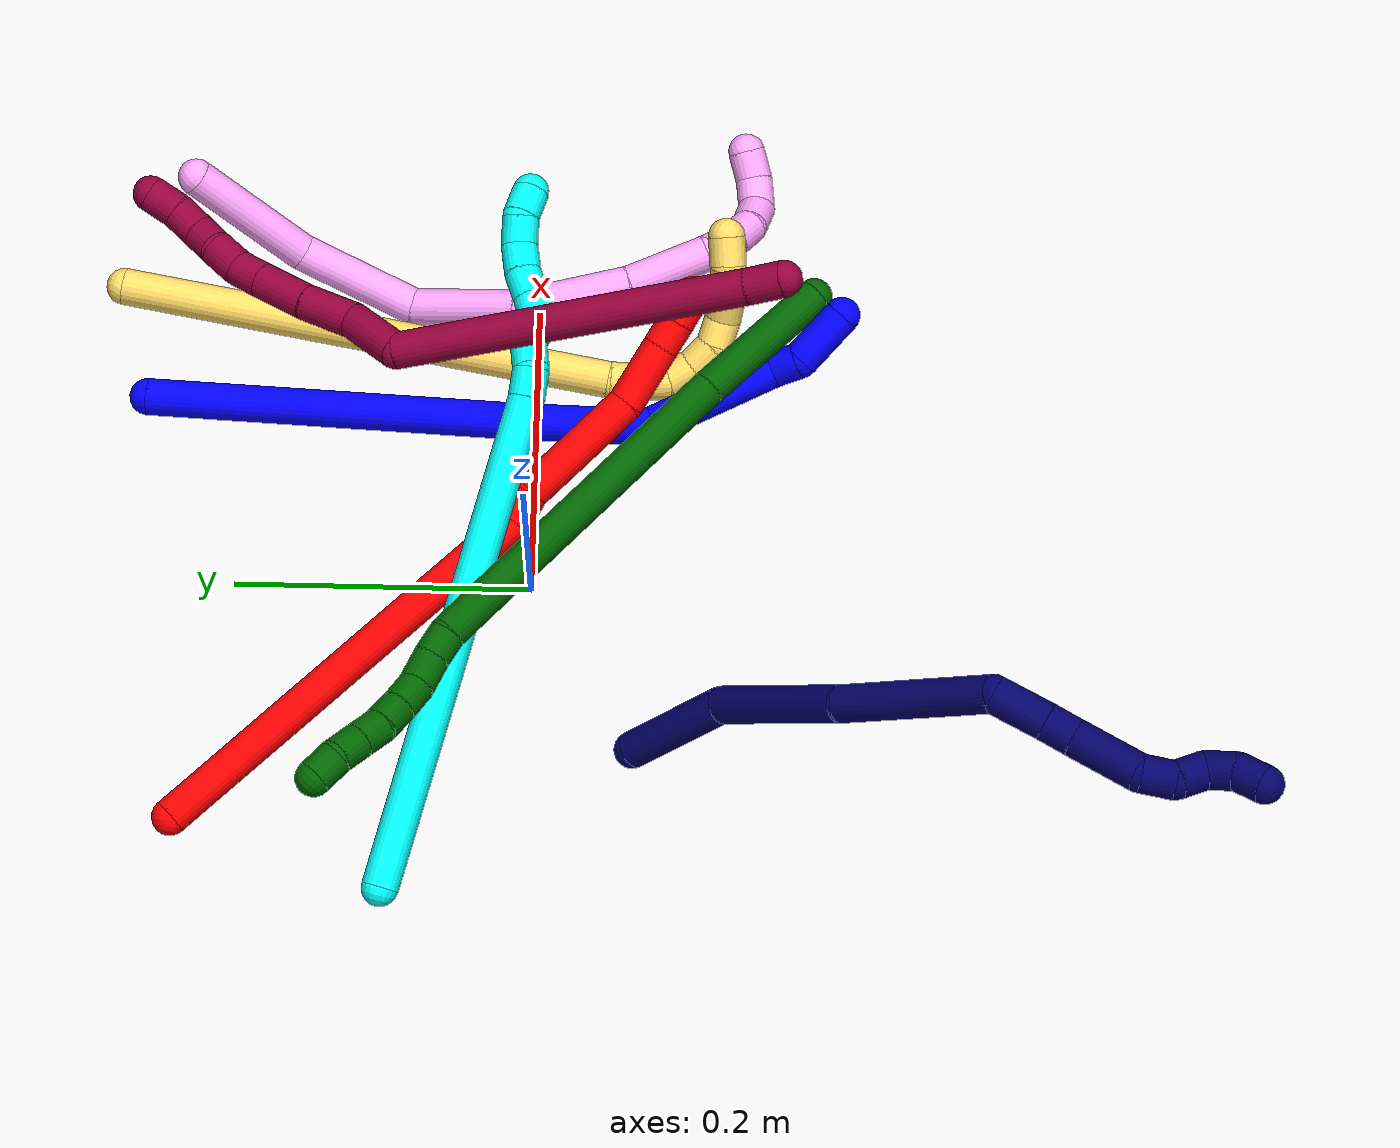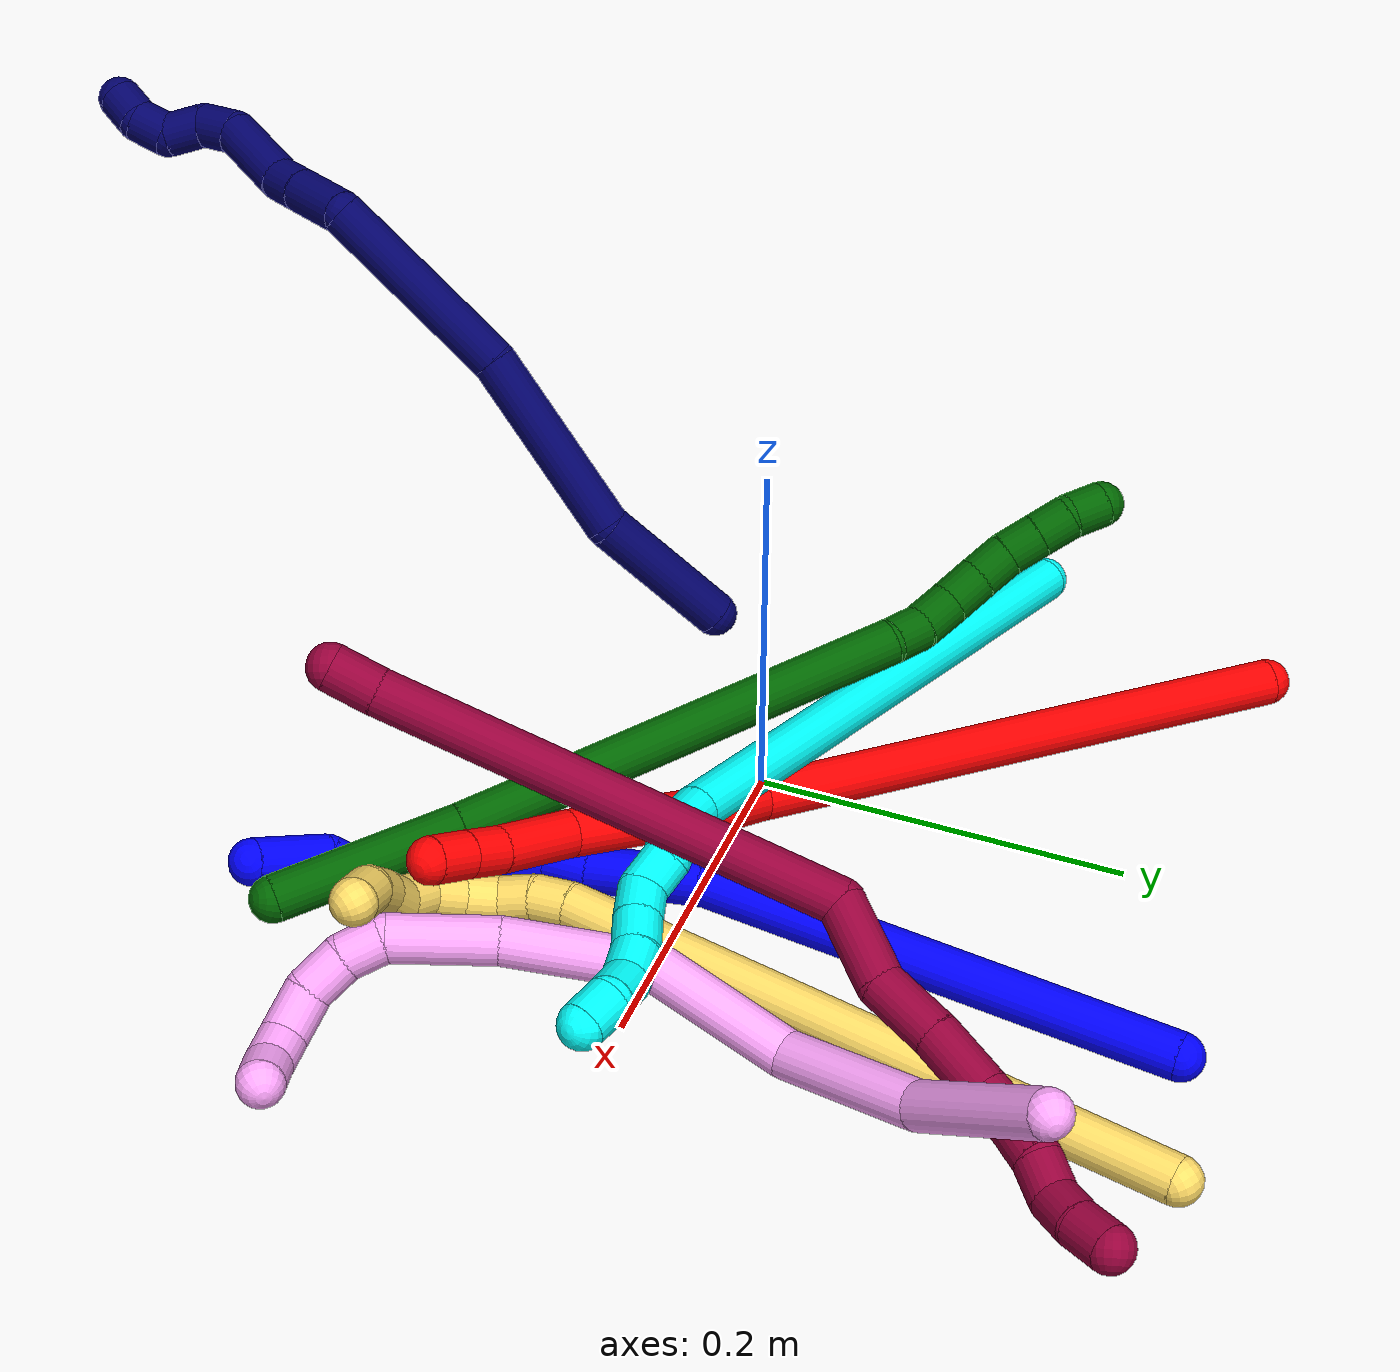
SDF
<sdf version="1.7">
 <world name="default">
  <plugin name="TubeGeneratorPlugin" filename="libtube_generator_plugin.so"/>
  <model name="photoneo_s_sensor">
   <static>1</static>
   <pose>0 0 2 1.57079 1.57079 3.14159</pose>
   <link name="link">
    <inertial><mass>0.1</mass></inertial>
    <sensor name="sensor" type="depth">
     <update_rate>30</update_rate>
     <camera>
      <horizontal_fov>1.22</horizontal_fov>
      <image><width>1920</width><height>1200</height><format>B8G8R8</format></image>
      <clip><near>0.1</near><far>4</far></clip>
      <depth_camera><output>points</output></depth_camera>
     </camera>
     <plugin name="camera_plugin" filename="libgazebo_ros_depth_camera.so">
      <baseline>0.2</baseline>
      <alwaysOn>1</alwaysOn>
      <updateRate>0.0</updateRate>
      <cameraName>camera_ir</cameraName>
      <imageTopicName>/camera/color/image_raw</imageTopicName>
      <cameraInfoTopicName>/camera/color/camera_info</cameraInfoTopicName>
      <depthImageTopicName>/camera/depth/image_raw</depthImageTopicName>
      <depthImageCameraInfoTopicName>/camera/depth/camera_info</depthImageCameraInfoTopicName>
      <pointCloudTopicName>/camera/depth/points</pointCloudTopicName>
      <frameName>fr_optical</frameName>
      <pointCloudCutoff>0.1</pointCloudCutoff>
      <pointCloudCutoffMax>2.0</pointCloudCutoffMax>
      <distortionK1>0</distortionK1>
      <distortionK2>0</distortionK2>
      <distortionK3>0</distortionK3>
      <distortionT1>0</distortionT1>
      <distortionT2>0</distortionT2>
      <CxPrime>0</CxPrime>
      <Cx>0</Cx>
      <Cy>0</Cy>
      <focalLength>0</focalLength>
      <hackBaseline>0</hackBaseline>
     </plugin>
    </sensor>
   </link>
  </model>
  <gravity>0 0 -9.8</gravity>
  <magnetic_field>6e-06 2.3e-05 -4.2e-05</magnetic_field>
  <atmosphere type="adiabatic"/>
  <physics name="default_physics" default="0" type="ode">
   <max_step_size>0.003</max_step_size>
   <real_time_factor>1</real_time_factor>
   <real_time_update_rate>1000</real_time_update_rate>
   <max_contacts>10000</max_contacts>
   <ode>
    <solver>
     <type>quick</type>
     <iters>100</iters>
     <sor>1.3</sor>
     <use_dynamic_moi_rescaling>0</use_dynamic_moi_rescaling>
    </solver>
    <constraints>
     <contact_max_correcting_vel>0</contact_max_correcting_vel>
     <contact_surface_layer>0.001</contact_surface_layer>
     <cfm>0</cfm>
     <erp>0.2</erp>
    </constraints>
   </ode>
  </physics>
  <scene><ambient>0.4 0.4 0.4 1</ambient><background>0.7 0.7 0.7 1</background><shadows>0</shadows></scene>
  <audio><device>default</device></audio>
  <spherical_coordinates>
   <surface_model>EARTH_WGS84</surface_model>
   <latitude_deg>0</latitude_deg>
   <longitude_deg>0</longitude_deg>
   <elevation>0</elevation>
   <heading_deg>0</heading_deg>
  </spherical_coordinates>
  <model name="bin">
   <static>1</static>
   <link name="bottom">
    <collision name="collision-bottom">
     <pose>0 0 -0.01 0 -0 0</pose>
     <geometry><box><size>0.8 0.6 0.02</size></box></geometry>
     <surface>
      <friction><ode><mu>100</mu><mu2>100</mu2></ode></friction>
      <contact><collide_bitmask>65535</collide_bitmask></contact>
     </surface>
    </collision>
   </link>
   <link name="west_wall">
    <collision name="collision-west_wall">
     <pose>-0.41 0 0.1 0 -0 0</pose>
     <geometry><box><size>0.02 0.6 0.2</size></box></geometry>
     <surface>
      <friction><ode><mu>100</mu><mu2>100</mu2></ode></friction>
      <contact><collide_bitmask>65535</collide_bitmask></contact>
     </surface>
    </collision>
   </link>
   <link name="east_wall">
    <collision name="collision-east_wall">
     <pose>0.41 0 0.1 0 -0 0</pose>
     <geometry><box><size>0.02 0.6 0.2</size></box></geometry>
     <surface>
      <friction><ode><mu>100</mu><mu2>100</mu2></ode></friction>
      <contact><collide_bitmask>65535</collide_bitmask></contact>
     </surface>
    </collision>
   </link>
   <link name="south_wall">
    <collision name="collision-south_wall">
     <pose>0 -0.31 0.1 0 -0 0</pose>
     <geometry><box><size>0.8 0.02 0.2</size></box></geometry>
     <surface>
      <friction><ode><mu>100</mu><mu2>100</mu2></ode></friction>
      <contact><collide_bitmask>65535</collide_bitmask></contact>
     </surface>
    </collision>
   </link>
   <link name="north_wall">
    <collision name="collision-north_wall">
     <pose>0 0.31 0.1 0 -0 0</pose>
     <geometry><box><size>0.8 0.02 0.2</size></box></geometry>
     <surface>
      <friction><ode><mu>100</mu><mu2>100</mu2></ode></friction>
      <contact><collide_bitmask>65535</collide_bitmask></contact>
     </surface>
    </collision>
   </link>
  </model>
  <model name="1">
   <static>0</static>
   <link name="1">
    <collision name="collision-cylinder-e_1_1_4">
     <pose>-0.019524 -0.123714 -0.022829 1.75327 -0.153968 -0.184817</pose>
     <geometry><cylinder><radius>0.0125</radius><length>0.254617</length></cylinder></geometry>
     <surface>
      <friction><ode><mu>1.16</mu><mu2>1.16</mu2><slip1>0</slip1><slip2>0</slip2></ode></friction>
      <contact><ode><kp>1e+06</kp><kd>1</kd><max_vel>0</max_vel><min_depth>0.001</min_depth></ode></contact>
     </surface>
    </collision>
    <visual name="visual-cylinder-e_1_1_4">
     <pose>-0.019524 -0.123714 -0.022829 1.75327 -0.153968 -0.184817</pose>
     <geometry><cylinder><radius>0.0125</radius><length>0.254617</length></cylinder></geometry>
     <material><ambient>0 0 1 1</ambient></material>
    </visual>
    <collision name="collision-cylinder-e_2_4_5">
     <pose>-0.037356 -0.277705 -0.054375 1.85114 0.053669 0.071289</pose>
     <geometry><cylinder><radius>0.0125</radius><length>0.063104</length></cylinder></geometry>
     <surface>
      <friction><ode><mu>1.16</mu><mu2>1.16</mu2><slip1>0</slip1><slip2>0</slip2></ode></friction>
      <contact><ode><kp>1e+06</kp><kd>1</kd><max_vel>0</max_vel><min_depth>0.001</min_depth></ode></contact>
     </surface>
    </collision>
    <visual name="visual-cylinder-e_2_4_5">
     <pose>-0.037356 -0.277705 -0.054375 1.85114 0.053669 0.071289</pose>
     <geometry><cylinder><radius>0.0125</radius><length>0.063104</length></cylinder></geometry>
     <material><ambient>0 0 1 1</ambient></material>
    </visual>
    <collision name="collision-cylinder-e_3_5_6">
     <pose>-0.036421 -0.320778 -0.065133 1.72892 -0.05843 -0.068478</pose>
     <geometry><cylinder><radius>0.0125</radius><length>0.025962</length></cylinder></geometry>
     <surface>
      <friction><ode><mu>1.16</mu><mu2>1.16</mu2><slip1>0</slip1><slip2>0</slip2></ode></friction>
      <contact><ode><kp>1e+06</kp><kd>1</kd><max_vel>0</max_vel><min_depth>0.001</min_depth></ode></contact>
     </surface>
    </collision>
    <visual name="visual-cylinder-e_3_5_6">
     <pose>-0.036421 -0.320778 -0.065133 1.72892 -0.05843 -0.068478</pose>
     <geometry><cylinder><radius>0.0125</radius><length>0.025962</length></cylinder></geometry>
     <material><ambient>0 0 1 1</ambient></material>
    </visual>
    <collision name="collision-cylinder-e_4_6_7">
     <pose>-0.021456 -0.377392 -0.062992 1.47566 0.343093 0.31244</pose>
     <geometry><cylinder><radius>0.0125</radius><length>0.093479</length></cylinder></geometry>
     <surface>
      <friction><ode><mu>1.16</mu><mu2>1.16</mu2><slip1>0</slip1><slip2>0</slip2></ode></friction>
      <contact><ode><kp>1e+06</kp><kd>1</kd><max_vel>0</max_vel><min_depth>0.001</min_depth></ode></contact>
     </surface>
    </collision>
    <visual name="visual-cylinder-e_4_6_7">
     <pose>-0.021456 -0.377392 -0.062992 1.47566 0.343093 0.31244</pose>
     <geometry><cylinder><radius>0.0125</radius><length>0.093479</length></cylinder></geometry>
     <material><ambient>0 0 1 1</ambient></material>
    </visual>
    <collision name="collision-cylinder-e_5_7_8">
     <pose>-0.00827 -0.431105 -0.055356 1.23495 -0.237482 -0.169031</pose>
     <geometry><cylinder><radius>0.0125</radius><length>0.02157</length></cylinder></geometry>
     <surface>
      <friction><ode><mu>1.16</mu><mu2>1.16</mu2><slip1>0</slip1><slip2>0</slip2></ode></friction>
      <contact><ode><kp>1e+06</kp><kd>1</kd><max_vel>0</max_vel><min_depth>0.001</min_depth></ode></contact>
     </surface>
    </collision>
    <visual name="visual-cylinder-e_5_7_8">
     <pose>-0.00827 -0.431105 -0.055356 1.23495 -0.237482 -0.169031</pose>
     <geometry><cylinder><radius>0.0125</radius><length>0.02157</length></cylinder></geometry>
     <material><ambient>0 0 1 1</ambient></material>
    </visual>
    <collision name="collision-cylinder-e_6_8_2">
     <pose>-0.004569 -0.457379 -0.041009 0.983873 0.307126 0.165509</pose>
     <geometry><cylinder><radius>0.0125</radius><length>0.041267</length></cylinder></geometry>
     <surface>
      <friction><ode><mu>1.16</mu><mu2>1.16</mu2><slip1>0</slip1><slip2>0</slip2></ode></friction>
      <contact><ode><kp>1e+06</kp><kd>1</kd><max_vel>0</max_vel><min_depth>0.001</min_depth></ode></contact>
     </surface>
    </collision>
    <visual name="visual-cylinder-e_6_8_2">
     <pose>-0.004569 -0.457379 -0.041009 0.983873 0.307126 0.165509</pose>
     <geometry><cylinder><radius>0.0125</radius><length>0.041267</length></cylinder></geometry>
     <material><ambient>0 0 1 1</ambient></material>
    </visual>
    <collision name="collision-sphere-2">
     <pose>0.001669 -0.473755 -0.030117 0 -0 0</pose>
     <geometry><sphere><radius>0.0125</radius></sphere></geometry>
     <surface>
      <friction><ode><mu>1.16</mu><mu2>1.16</mu2><slip1>0</slip1><slip2>0</slip2></ode></friction>
      <contact><ode><kp>1e+06</kp><kd>1</kd><max_vel>0</max_vel><min_depth>0.001</min_depth></ode></contact>
     </surface>
    </collision>
    <visual name="visual-sphere-2">
     <pose>0.001669 -0.473755 -0.030117 0 -0 0</pose>
     <geometry><sphere><radius>0.0125</radius></sphere></geometry>
     <material><ambient>0 0 1 1</ambient></material>
    </visual>
    <collision name="collision-sphere-4">
     <pose>-0.039048 -0.247428 -0.045657 0 -0 0</pose>
     <geometry><sphere><radius>0.0125</radius></sphere></geometry>
     <surface>
      <friction><ode><mu>1.16</mu><mu2>1.16</mu2><slip1>0</slip1><slip2>0</slip2></ode></friction>
      <contact><ode><kp>1e+06</kp><kd>1</kd><max_vel>0</max_vel><min_depth>0.001</min_depth></ode></contact>
     </surface>
    </collision>
    <visual name="visual-sphere-4">
     <pose>-0.039048 -0.247428 -0.045657 0 -0 0</pose>
     <geometry><sphere><radius>0.0125</radius></sphere></geometry>
     <material><ambient>0 0 1 1</ambient></material>
    </visual>
    <collision name="collision-sphere-1">
     <geometry><sphere><radius>0.0125</radius></sphere></geometry>
     <surface>
      <friction><ode><mu>1.16</mu><mu2>1.16</mu2><slip1>0</slip1><slip2>0</slip2></ode></friction>
      <contact><ode><kp>1e+06</kp><kd>1</kd><max_vel>0</max_vel><min_depth>0.001</min_depth></ode></contact>
     </surface>
    </collision>
    <visual name="visual-sphere-1">
     <geometry><sphere><radius>0.0125</radius></sphere></geometry>
     <material><ambient>0 0 1 1</ambient></material>
    </visual>
    <collision name="collision-sphere-8">
     <pose>-0.010807 -0.441002 -0.051901 0 -0 0</pose>
     <geometry><sphere><radius>0.0125</radius></sphere></geometry>
     <surface>
      <friction><ode><mu>1.16</mu><mu2>1.16</mu2><slip1>0</slip1><slip2>0</slip2></ode></friction>
      <contact><ode><kp>1e+06</kp><kd>1</kd><max_vel>0</max_vel><min_depth>0.001</min_depth></ode></contact>
     </surface>
    </collision>
    <visual name="visual-sphere-8">
     <pose>-0.010807 -0.441002 -0.051901 0 -0 0</pose>
     <geometry><sphere><radius>0.0125</radius></sphere></geometry>
     <material><ambient>0 0 1 1</ambient></material>
    </visual>
    <collision name="collision-sphere-5">
     <pose>-0.035663 -0.307981 -0.063092 0 -0 0</pose>
     <geometry><sphere><radius>0.0125</radius></sphere></geometry>
     <surface>
      <friction><ode><mu>1.16</mu><mu2>1.16</mu2><slip1>0</slip1><slip2>0</slip2></ode></friction>
      <contact><ode><kp>1e+06</kp><kd>1</kd><max_vel>0</max_vel><min_depth>0.001</min_depth></ode></contact>
     </surface>
    </collision>
    <visual name="visual-sphere-5">
     <pose>-0.035663 -0.307981 -0.063092 0 -0 0</pose>
     <geometry><sphere><radius>0.0125</radius></sphere></geometry>
     <material><ambient>0 0 1 1</ambient></material>
    </visual>
    <collision name="collision-sphere-6">
     <pose>-0.037179 -0.333575 -0.067173 0 -0 0</pose>
     <geometry><sphere><radius>0.0125</radius></sphere></geometry>
     <surface>
      <friction><ode><mu>1.16</mu><mu2>1.16</mu2><slip1>0</slip1><slip2>0</slip2></ode></friction>
      <contact><ode><kp>1e+06</kp><kd>1</kd><max_vel>0</max_vel><min_depth>0.001</min_depth></ode></contact>
     </surface>
    </collision>
    <visual name="visual-sphere-6">
     <pose>-0.037179 -0.333575 -0.067173 0 -0 0</pose>
     <geometry><sphere><radius>0.0125</radius></sphere></geometry>
     <material><ambient>0 0 1 1</ambient></material>
    </visual>
    <collision name="collision-sphere-7">
     <pose>-0.005733 -0.421208 -0.058811 0 -0 0</pose>
     <geometry><sphere><radius>0.0125</radius></sphere></geometry>
     <surface>
      <friction><ode><mu>1.16</mu><mu2>1.16</mu2><slip1>0</slip1><slip2>0</slip2></ode></friction>
      <contact><ode><kp>1e+06</kp><kd>1</kd><max_vel>0</max_vel><min_depth>0.001</min_depth></ode></contact>
     </surface>
    </collision>
    <visual name="visual-sphere-7">
     <pose>-0.005733 -0.421208 -0.058811 0 -0 0</pose>
     <geometry><sphere><radius>0.0125</radius></sphere></geometry>
     <material><ambient>0 0 1 1</ambient></material>
    </visual>
    <inertial>
     <pose>-0.021293 -0.241608 -0.039419 0 -0 0</pose>
     <mass>0.5</mass>
     <inertia>
      <ixx>0.001216</ixx>
      <ixy>0</ixy>
      <ixz>0</ixz>
      <iyy>-0.000462</iyy>
      <iyz>0</iyz>
      <izz>0.001629</izz>
     </inertia>
    </inertial>
   </link>
   <pose>0.129156 0.264764 0.011497 -0.127699 0.685093 0.086068</pose>
  </model>
  <model name="2">
   <static>0</static>
   <link name="2">
    <collision name="collision-cylinder-e_1_1_4">
     <pose>0.005657 -0.094956 -0.117462 2.46175 0.037437 0.105775</pose>
     <geometry><cylinder><radius>0.0125</radius><length>0.302297</length></cylinder></geometry>
     <surface>
      <friction><ode><mu>1.16</mu><mu2>1.16</mu2><slip1>0</slip1><slip2>0</slip2></ode></friction>
      <contact><ode><kp>1e+06</kp><kd>1</kd><max_vel>0</max_vel><min_depth>0.001</min_depth></ode></contact>
     </surface>
    </collision>
    <visual name="visual-cylinder-e_1_1_4">
     <pose>0.005657 -0.094956 -0.117462 2.46175 0.037437 0.105775</pose>
     <geometry><cylinder><radius>0.0125</radius><length>0.302297</length></cylinder></geometry>
     <material><ambient>1 0 0 1</ambient></material>
    </visual>
    <collision name="collision-cylinder-e_2_4_5">
     <pose>0.013407 -0.193536 -0.245707 2.81731 0.181901 1.01724</pose>
     <geometry><cylinder><radius>0.0125</radius><length>0.023133</length></cylinder></geometry>
     <surface>
      <friction><ode><mu>1.16</mu><mu2>1.16</mu2><slip1>0</slip1><slip2>0</slip2></ode></friction>
      <contact><ode><kp>1e+06</kp><kd>1</kd><max_vel>0</max_vel><min_depth>0.001</min_depth></ode></contact>
     </surface>
    </collision>
    <visual name="visual-cylinder-e_2_4_5">
     <pose>0.013407 -0.193536 -0.245707 2.81731 0.181901 1.01724</pose>
     <geometry><cylinder><radius>0.0125</radius><length>0.023133</length></cylinder></geometry>
     <material><ambient>1 0 0 1</ambient></material>
    </visual>
    <collision name="collision-cylinder-e_3_5_6">
     <pose>0.020701 -0.223216 -0.291618 2.50342 0.118365 0.354921</pose>
     <geometry><cylinder><radius>0.0125</radius><length>0.088088</length></cylinder></geometry>
     <surface>
      <friction><ode><mu>1.16</mu><mu2>1.16</mu2><slip1>0</slip1><slip2>0</slip2></ode></friction>
      <contact><ode><kp>1e+06</kp><kd>1</kd><max_vel>0</max_vel><min_depth>0.001</min_depth></ode></contact>
     </surface>
    </collision>
    <visual name="visual-cylinder-e_3_5_6">
     <pose>0.020701 -0.223216 -0.291618 2.50342 0.118365 0.354921</pose>
     <geometry><cylinder><radius>0.0125</radius><length>0.088088</length></cylinder></geometry>
     <material><ambient>1 0 0 1</ambient></material>
    </visual>
    <collision name="collision-cylinder-e_4_6_7">
     <pose>0.030174 -0.257177 -0.347206 2.77283 0.192346 0.954723</pose>
     <geometry><cylinder><radius>0.0125</radius><length>0.044694</length></cylinder></geometry>
     <surface>
      <friction><ode><mu>1.16</mu><mu2>1.16</mu2><slip1>0</slip1><slip2>0</slip2></ode></friction>
      <contact><ode><kp>1e+06</kp><kd>1</kd><max_vel>0</max_vel><min_depth>0.001</min_depth></ode></contact>
     </surface>
    </collision>
    <visual name="visual-cylinder-e_4_6_7">
     <pose>0.030174 -0.257177 -0.347206 2.77283 0.192346 0.954723</pose>
     <geometry><cylinder><radius>0.0125</radius><length>0.044694</length></cylinder></geometry>
     <material><ambient>1 0 0 1</ambient></material>
    </visual>
    <collision name="collision-cylinder-e_5_7_8">
     <pose>0.037202 -0.268607 -0.376773 2.77249 0.275183 1.2764</pose>
     <geometry><cylinder><radius>0.0125</radius><length>0.020293</length></cylinder></geometry>
     <surface>
      <friction><ode><mu>1.16</mu><mu2>1.16</mu2><slip1>0</slip1><slip2>0</slip2></ode></friction>
      <contact><ode><kp>1e+06</kp><kd>1</kd><max_vel>0</max_vel><min_depth>0.001</min_depth></ode></contact>
     </surface>
    </collision>
    <visual name="visual-cylinder-e_5_7_8">
     <pose>0.037202 -0.268607 -0.376773 2.77249 0.275183 1.2764</pose>
     <geometry><cylinder><radius>0.0125</radius><length>0.020293</length></cylinder></geometry>
     <material><ambient>1 0 0 1</ambient></material>
    </visual>
    <collision name="collision-cylinder-e_6_8_2">
     <pose>0.042664 -0.27573 -0.395639 2.78818 0.254413 1.24307</pose>
     <geometry><cylinder><radius>0.0125</radius><length>0.021494</length></cylinder></geometry>
     <surface>
      <friction><ode><mu>1.16</mu><mu2>1.16</mu2><slip1>0</slip1><slip2>0</slip2></ode></friction>
      <contact><ode><kp>1e+06</kp><kd>1</kd><max_vel>0</max_vel><min_depth>0.001</min_depth></ode></contact>
     </surface>
    </collision>
    <visual name="visual-cylinder-e_6_8_2">
     <pose>0.042664 -0.27573 -0.395639 2.78818 0.254413 1.24307</pose>
     <geometry><cylinder><radius>0.0125</radius><length>0.021494</length></cylinder></geometry>
     <material><ambient>1 0 0 1</ambient></material>
    </visual>
    <collision name="collision-sphere-2">
     <pose>0.045369 -0.27933 -0.405397 0 -0 0</pose>
     <geometry><sphere><radius>0.0125</radius></sphere></geometry>
     <surface>
      <friction><ode><mu>1.16</mu><mu2>1.16</mu2><slip1>0</slip1><slip2>0</slip2></ode></friction>
      <contact><ode><kp>1e+06</kp><kd>1</kd><max_vel>0</max_vel><min_depth>0.001</min_depth></ode></contact>
     </surface>
    </collision>
    <visual name="visual-sphere-2">
     <pose>0.045369 -0.27933 -0.405397 0 -0 0</pose>
     <geometry><sphere><radius>0.0125</radius></sphere></geometry>
     <material><ambient>1 0 0 1</ambient></material>
    </visual>
    <collision name="collision-sphere-4">
     <pose>0.011315 -0.189912 -0.234924 0 -0 0</pose>
     <geometry><sphere><radius>0.0125</radius></sphere></geometry>
     <surface>
      <friction><ode><mu>1.16</mu><mu2>1.16</mu2><slip1>0</slip1><slip2>0</slip2></ode></friction>
      <contact><ode><kp>1e+06</kp><kd>1</kd><max_vel>0</max_vel><min_depth>0.001</min_depth></ode></contact>
     </surface>
    </collision>
    <visual name="visual-sphere-4">
     <pose>0.011315 -0.189912 -0.234924 0 -0 0</pose>
     <geometry><sphere><radius>0.0125</radius></sphere></geometry>
     <material><ambient>1 0 0 1</ambient></material>
    </visual>
    <collision name="collision-sphere-1">
     <geometry><sphere><radius>0.0125</radius></sphere></geometry>
     <surface>
      <friction><ode><mu>1.16</mu><mu2>1.16</mu2><slip1>0</slip1><slip2>0</slip2></ode></friction>
      <contact><ode><kp>1e+06</kp><kd>1</kd><max_vel>0</max_vel><min_depth>0.001</min_depth></ode></contact>
     </surface>
    </collision>
    <visual name="visual-sphere-1">
     <geometry><sphere><radius>0.0125</radius></sphere></geometry>
     <material><ambient>1 0 0 1</ambient></material>
    </visual>
    <collision name="collision-sphere-8">
     <pose>0.039959 -0.27213 -0.38588 0 -0 0</pose>
     <geometry><sphere><radius>0.0125</radius></sphere></geometry>
     <surface>
      <friction><ode><mu>1.16</mu><mu2>1.16</mu2><slip1>0</slip1><slip2>0</slip2></ode></friction>
      <contact><ode><kp>1e+06</kp><kd>1</kd><max_vel>0</max_vel><min_depth>0.001</min_depth></ode></contact>
     </surface>
    </collision>
    <visual name="visual-sphere-8">
     <pose>0.039959 -0.27213 -0.38588 0 -0 0</pose>
     <geometry><sphere><radius>0.0125</radius></sphere></geometry>
     <material><ambient>1 0 0 1</ambient></material>
    </visual>
    <collision name="collision-sphere-5">
     <pose>0.015499 -0.197161 -0.25649 0 -0 0</pose>
     <geometry><sphere><radius>0.0125</radius></sphere></geometry>
     <surface>
      <friction><ode><mu>1.16</mu><mu2>1.16</mu2><slip1>0</slip1><slip2>0</slip2></ode></friction>
      <contact><ode><kp>1e+06</kp><kd>1</kd><max_vel>0</max_vel><min_depth>0.001</min_depth></ode></contact>
     </surface>
    </collision>
    <visual name="visual-sphere-5">
     <pose>0.015499 -0.197161 -0.25649 0 -0 0</pose>
     <geometry><sphere><radius>0.0125</radius></sphere></geometry>
     <material><ambient>1 0 0 1</ambient></material>
    </visual>
    <collision name="collision-sphere-6">
     <pose>0.025902 -0.24927 -0.326746 0 -0 0</pose>
     <geometry><sphere><radius>0.0125</radius></sphere></geometry>
     <surface>
      <friction><ode><mu>1.16</mu><mu2>1.16</mu2><slip1>0</slip1><slip2>0</slip2></ode></friction>
      <contact><ode><kp>1e+06</kp><kd>1</kd><max_vel>0</max_vel><min_depth>0.001</min_depth></ode></contact>
     </surface>
    </collision>
    <visual name="visual-sphere-6">
     <pose>0.025902 -0.24927 -0.326746 0 -0 0</pose>
     <geometry><sphere><radius>0.0125</radius></sphere></geometry>
     <material><ambient>1 0 0 1</ambient></material>
    </visual>
    <collision name="collision-sphere-7">
     <pose>0.034445 -0.265084 -0.367666 0 -0 0</pose>
     <geometry><sphere><radius>0.0125</radius></sphere></geometry>
     <surface>
      <friction><ode><mu>1.16</mu><mu2>1.16</mu2><slip1>0</slip1><slip2>0</slip2></ode></friction>
      <contact><ode><kp>1e+06</kp><kd>1</kd><max_vel>0</max_vel><min_depth>0.001</min_depth></ode></contact>
     </surface>
    </collision>
    <visual name="visual-sphere-7">
     <pose>0.034445 -0.265084 -0.367666 0 -0 0</pose>
     <geometry><sphere><radius>0.0125</radius></sphere></geometry>
     <material><ambient>1 0 0 1</ambient></material>
    </visual>
    <inertial>
     <pose>0.013729 -0.151433 -0.197097 0 -0 0</pose>
     <mass>0.5</mass>
     <inertia>
      <ixx>0.002643</ixx>
      <ixy>0</ixy>
      <ixz>0</ixz>
      <iyy>-0.001579</iyy>
      <iyz>0</iyz>
      <izz>0.001366</izz>
     </inertia>
    </inertial>
   </link>
   <pose>-0.166292 0.23387 0.012395 2.27134 -1.31508 -2.40078</pose>
  </model>
  <model name="3">
   <static>0</static>
   <link name="3">
    <collision name="collision-cylinder-e_1_1_4">
     <pose>0.030661 0.008361 0.166868 -0.050066 0.181495 -0.004557</pose>
     <geometry><cylinder><radius>0.0125</radius><length>0.339734</length></cylinder></geometry>
     <surface>
      <friction><ode><mu>1.16</mu><mu2>1.16</mu2><slip1>0</slip1><slip2>0</slip2></ode></friction>
      <contact><ode><kp>1e+06</kp><kd>1</kd><max_vel>0</max_vel><min_depth>0.001</min_depth></ode></contact>
     </surface>
    </collision>
    <visual name="visual-cylinder-e_1_1_4">
     <pose>0.030661 0.008361 0.166868 -0.050066 0.181495 -0.004557</pose>
     <geometry><cylinder><radius>0.0125</radius><length>0.339734</length></cylinder></geometry>
     <material><ambient>0.003922 1 0.996078 1</ambient></material>
    </visual>
    <collision name="collision-cylinder-e_2_4_5">
     <pose>0.06275 0.018568 0.343548 -0.185873 0.142025 -0.01326</pose>
     <geometry><cylinder><radius>0.0125</radius><length>0.020171</length></cylinder></geometry>
     <surface>
      <friction><ode><mu>1.16</mu><mu2>1.16</mu2><slip1>0</slip1><slip2>0</slip2></ode></friction>
      <contact><ode><kp>1e+06</kp><kd>1</kd><max_vel>0</max_vel><min_depth>0.001</min_depth></ode></contact>
     </surface>
    </collision>
    <visual name="visual-cylinder-e_2_4_5">
     <pose>0.06275 0.018568 0.343548 -0.185873 0.142025 -0.01326</pose>
     <geometry><cylinder><radius>0.0125</radius><length>0.020171</length></cylinder></geometry>
     <material><ambient>0.003922 1 0.996078 1</ambient></material>
    </visual>
    <collision name="collision-cylinder-e_3_5_6">
     <pose>0.067405 0.025483 0.361407 -0.56221 0.327114 -0.095234</pose>
     <geometry><cylinder><radius>0.0125</radius><length>0.020088</length></cylinder></geometry>
     <surface>
      <friction><ode><mu>1.16</mu><mu2>1.16</mu2><slip1>0</slip1><slip2>0</slip2></ode></friction>
      <contact><ode><kp>1e+06</kp><kd>1</kd><max_vel>0</max_vel><min_depth>0.001</min_depth></ode></contact>
     </surface>
    </collision>
    <visual name="visual-cylinder-e_3_5_6">
     <pose>0.067405 0.025483 0.361407 -0.56221 0.327114 -0.095234</pose>
     <geometry><cylinder><radius>0.0125</radius><length>0.020088</length></cylinder></geometry>
     <material><ambient>0.003922 1 0.996078 1</ambient></material>
    </visual>
    <collision name="collision-cylinder-e_4_6_7">
     <pose>0.077582 0.032336 0.376423 -0.250464 0.768172 -0.101672</pose>
     <geometry><cylinder><radius>0.0125</radius><length>0.020004</length></cylinder></geometry>
     <surface>
      <friction><ode><mu>1.16</mu><mu2>1.16</mu2><slip1>0</slip1><slip2>0</slip2></ode></friction>
      <contact><ode><kp>1e+06</kp><kd>1</kd><max_vel>0</max_vel><min_depth>0.001</min_depth></ode></contact>
     </surface>
    </collision>
    <visual name="visual-cylinder-e_4_6_7">
     <pose>0.077582 0.032336 0.376423 -0.250464 0.768172 -0.101672</pose>
     <geometry><cylinder><radius>0.0125</radius><length>0.020004</length></cylinder></geometry>
     <material><ambient>0.003922 1 0.996078 1</ambient></material>
    </visual>
    <collision name="collision-cylinder-e_5_7_8">
     <pose>0.086678 0.040128 0.391092 -0.662719 0.216389 -0.074704</pose>
     <geometry><cylinder><radius>0.0125</radius><length>0.020001</length></cylinder></geometry>
     <surface>
      <friction><ode><mu>1.16</mu><mu2>1.16</mu2><slip1>0</slip1><slip2>0</slip2></ode></friction>
      <contact><ode><kp>1e+06</kp><kd>1</kd><max_vel>0</max_vel><min_depth>0.001</min_depth></ode></contact>
     </surface>
    </collision>
    <visual name="visual-cylinder-e_5_7_8">
     <pose>0.086678 0.040128 0.391092 -0.662719 0.216389 -0.074704</pose>
     <geometry><cylinder><radius>0.0125</radius><length>0.020001</length></cylinder></geometry>
     <material><ambient>0.003922 1 0.996078 1</ambient></material>
    </visual>
    <collision name="collision-cylinder-e_6_8_9">
     <pose>0.0904 0.052677 0.406192 -0.723713 0.158083 -0.059945</pose>
     <geometry><cylinder><radius>0.0125</radius><length>0.020001</length></cylinder></geometry>
     <surface>
      <friction><ode><mu>1.16</mu><mu2>1.16</mu2><slip1>0</slip1><slip2>0</slip2></ode></friction>
      <contact><ode><kp>1e+06</kp><kd>1</kd><max_vel>0</max_vel><min_depth>0.001</min_depth></ode></contact>
     </surface>
    </collision>
    <visual name="visual-cylinder-e_6_8_9">
     <pose>0.0904 0.052677 0.406192 -0.723713 0.158083 -0.059945</pose>
     <geometry><cylinder><radius>0.0125</radius><length>0.020001</length></cylinder></geometry>
     <material><ambient>0.003922 1 0.996078 1</ambient></material>
    </visual>
    <collision name="collision-cylinder-e_7_9_10">
     <pose>0.094016 0.064096 0.42208 -0.521705 0.205601 -0.055062</pose>
     <geometry><cylinder><radius>0.0125</radius><length>0.02</length></cylinder></geometry>
     <surface>
      <friction><ode><mu>1.16</mu><mu2>1.16</mu2><slip1>0</slip1><slip2>0</slip2></ode></friction>
      <contact><ode><kp>1e+06</kp><kd>1</kd><max_vel>0</max_vel><min_depth>0.001</min_depth></ode></contact>
     </surface>
    </collision>
    <visual name="visual-cylinder-e_7_9_10">
     <pose>0.094016 0.064096 0.42208 -0.521705 0.205601 -0.055062</pose>
     <geometry><cylinder><radius>0.0125</radius><length>0.02</length></cylinder></geometry>
     <material><ambient>0.003922 1 0.996078 1</ambient></material>
    </visual>
    <collision name="collision-cylinder-e_8_10_11">
     <pose>0.096128 0.071299 0.440293 -0.234581 0.007109 -0.000838</pose>
     <geometry><cylinder><radius>0.0125</radius><length>0.02</length></cylinder></geometry>
     <surface>
      <friction><ode><mu>1.16</mu><mu2>1.16</mu2><slip1>0</slip1><slip2>0</slip2></ode></friction>
      <contact><ode><kp>1e+06</kp><kd>1</kd><max_vel>0</max_vel><min_depth>0.001</min_depth></ode></contact>
     </surface>
    </collision>
    <visual name="visual-cylinder-e_8_10_11">
     <pose>0.096128 0.071299 0.440293 -0.234581 0.007109 -0.000838</pose>
     <geometry><cylinder><radius>0.0125</radius><length>0.02</length></cylinder></geometry>
     <material><ambient>0.003922 1 0.996078 1</ambient></material>
    </visual>
    <collision name="collision-cylinder-e_9_11_2">
     <pose>0.100562 0.074636 0.45896 -0.112889 0.451481 -0.025952</pose>
     <geometry><cylinder><radius>0.0125</radius><length>0.02</length></cylinder></geometry>
     <surface>
      <friction><ode><mu>1.16</mu><mu2>1.16</mu2><slip1>0</slip1><slip2>0</slip2></ode></friction>
      <contact><ode><kp>1e+06</kp><kd>1</kd><max_vel>0</max_vel><min_depth>0.001</min_depth></ode></contact>
     </surface>
    </collision>
    <visual name="visual-cylinder-e_9_11_2">
     <pose>0.100562 0.074636 0.45896 -0.112889 0.451481 -0.025952</pose>
     <geometry><cylinder><radius>0.0125</radius><length>0.02</length></cylinder></geometry>
     <material><ambient>0.003922 1 0.996078 1</ambient></material>
    </visual>
    <collision name="collision-sphere-2">
     <pose>0.104925 0.07565 0.4679 0 -0 0</pose>
     <geometry><sphere><radius>0.0125</radius></sphere></geometry>
     <surface>
      <friction><ode><mu>1.16</mu><mu2>1.16</mu2><slip1>0</slip1><slip2>0</slip2></ode></friction>
      <contact><ode><kp>1e+06</kp><kd>1</kd><max_vel>0</max_vel><min_depth>0.001</min_depth></ode></contact>
     </surface>
    </collision>
    <visual name="visual-sphere-2">
     <pose>0.104925 0.07565 0.4679 0 -0 0</pose>
     <geometry><sphere><radius>0.0125</radius></sphere></geometry>
     <material><ambient>0.003922 1 0.996078 1</ambient></material>
    </visual>
    <collision name="collision-sphere-11">
     <pose>0.096199 0.073623 0.450019 0 -0 0</pose>
     <geometry><sphere><radius>0.0125</radius></sphere></geometry>
     <surface>
      <friction><ode><mu>1.16</mu><mu2>1.16</mu2><slip1>0</slip1><slip2>0</slip2></ode></friction>
      <contact><ode><kp>1e+06</kp><kd>1</kd><max_vel>0</max_vel><min_depth>0.001</min_depth></ode></contact>
     </surface>
    </collision>
    <visual name="visual-sphere-11">
     <pose>0.096199 0.073623 0.450019 0 -0 0</pose>
     <geometry><sphere><radius>0.0125</radius></sphere></geometry>
     <material><ambient>0.003922 1 0.996078 1</ambient></material>
    </visual>
    <collision name="collision-sphere-10">
     <pose>0.096057 0.068974 0.430567 0 -0 0</pose>
     <geometry><sphere><radius>0.0125</radius></sphere></geometry>
     <surface>
      <friction><ode><mu>1.16</mu><mu2>1.16</mu2><slip1>0</slip1><slip2>0</slip2></ode></friction>
      <contact><ode><kp>1e+06</kp><kd>1</kd><max_vel>0</max_vel><min_depth>0.001</min_depth></ode></contact>
     </surface>
    </collision>
    <visual name="visual-sphere-10">
     <pose>0.096057 0.068974 0.430567 0 -0 0</pose>
     <geometry><sphere><radius>0.0125</radius></sphere></geometry>
     <material><ambient>0.003922 1 0.996078 1</ambient></material>
    </visual>
    <collision name="collision-sphere-9">
     <pose>0.091974 0.059217 0.413593 0 -0 0</pose>
     <geometry><sphere><radius>0.0125</radius></sphere></geometry>
     <surface>
      <friction><ode><mu>1.16</mu><mu2>1.16</mu2><slip1>0</slip1><slip2>0</slip2></ode></friction>
      <contact><ode><kp>1e+06</kp><kd>1</kd><max_vel>0</max_vel><min_depth>0.001</min_depth></ode></contact>
     </surface>
    </collision>
    <visual name="visual-sphere-9">
     <pose>0.091974 0.059217 0.413593 0 -0 0</pose>
     <geometry><sphere><radius>0.0125</radius></sphere></geometry>
     <material><ambient>0.003922 1 0.996078 1</ambient></material>
    </visual>
    <collision name="collision-sphere-4">
     <pose>0.061322 0.016723 0.333735 0 -0 0</pose>
     <geometry><sphere><radius>0.0125</radius></sphere></geometry>
     <surface>
      <friction><ode><mu>1.16</mu><mu2>1.16</mu2><slip1>0</slip1><slip2>0</slip2></ode></friction>
      <contact><ode><kp>1e+06</kp><kd>1</kd><max_vel>0</max_vel><min_depth>0.001</min_depth></ode></contact>
     </surface>
    </collision>
    <visual name="visual-sphere-4">
     <pose>0.061322 0.016723 0.333735 0 -0 0</pose>
     <geometry><sphere><radius>0.0125</radius></sphere></geometry>
     <material><ambient>0.003922 1 0.996078 1</ambient></material>
    </visual>
    <collision name="collision-sphere-1">
     <geometry><sphere><radius>0.0125</radius></sphere></geometry>
     <surface>
      <friction><ode><mu>1.16</mu><mu2>1.16</mu2><slip1>0</slip1><slip2>0</slip2></ode></friction>
      <contact><ode><kp>1e+06</kp><kd>1</kd><max_vel>0</max_vel><min_depth>0.001</min_depth></ode></contact>
     </surface>
    </collision>
    <visual name="visual-sphere-1">
     <geometry><sphere><radius>0.0125</radius></sphere></geometry>
     <material><ambient>0.003922 1 0.996078 1</ambient></material>
    </visual>
    <collision name="collision-sphere-8">
     <pose>0.088825 0.046138 0.398792 0 -0 0</pose>
     <geometry><sphere><radius>0.0125</radius></sphere></geometry>
     <surface>
      <friction><ode><mu>1.16</mu><mu2>1.16</mu2><slip1>0</slip1><slip2>0</slip2></ode></friction>
      <contact><ode><kp>1e+06</kp><kd>1</kd><max_vel>0</max_vel><min_depth>0.001</min_depth></ode></contact>
     </surface>
    </collision>
    <visual name="visual-sphere-8">
     <pose>0.088825 0.046138 0.398792 0 -0 0</pose>
     <geometry><sphere><radius>0.0125</radius></sphere></geometry>
     <material><ambient>0.003922 1 0.996078 1</ambient></material>
    </visual>
    <collision name="collision-sphere-5">
     <pose>0.064178 0.020413 0.35336 0 -0 0</pose>
     <geometry><sphere><radius>0.0125</radius></sphere></geometry>
     <surface>
      <friction><ode><mu>1.16</mu><mu2>1.16</mu2><slip1>0</slip1><slip2>0</slip2></ode></friction>
      <contact><ode><kp>1e+06</kp><kd>1</kd><max_vel>0</max_vel><min_depth>0.001</min_depth></ode></contact>
     </surface>
    </collision>
    <visual name="visual-sphere-5">
     <pose>0.064178 0.020413 0.35336 0 -0 0</pose>
     <geometry><sphere><radius>0.0125</radius></sphere></geometry>
     <material><ambient>0.003922 1 0.996078 1</ambient></material>
    </visual>
    <collision name="collision-sphere-6">
     <pose>0.070632 0.030553 0.369455 0 -0 0</pose>
     <geometry><sphere><radius>0.0125</radius></sphere></geometry>
     <surface>
      <friction><ode><mu>1.16</mu><mu2>1.16</mu2><slip1>0</slip1><slip2>0</slip2></ode></friction>
      <contact><ode><kp>1e+06</kp><kd>1</kd><max_vel>0</max_vel><min_depth>0.001</min_depth></ode></contact>
     </surface>
    </collision>
    <visual name="visual-sphere-6">
     <pose>0.070632 0.030553 0.369455 0 -0 0</pose>
     <geometry><sphere><radius>0.0125</radius></sphere></geometry>
     <material><ambient>0.003922 1 0.996078 1</ambient></material>
    </visual>
    <collision name="collision-sphere-7">
     <pose>0.084531 0.034119 0.383392 0 -0 0</pose>
     <geometry><sphere><radius>0.0125</radius></sphere></geometry>
     <surface>
      <friction><ode><mu>1.16</mu><mu2>1.16</mu2><slip1>0</slip1><slip2>0</slip2></ode></friction>
      <contact><ode><kp>1e+06</kp><kd>1</kd><max_vel>0</max_vel><min_depth>0.001</min_depth></ode></contact>
     </surface>
    </collision>
    <visual name="visual-sphere-7">
     <pose>0.084531 0.034119 0.383392 0 -0 0</pose>
     <geometry><sphere><radius>0.0125</radius></sphere></geometry>
     <material><ambient>0.003922 1 0.996078 1</ambient></material>
    </visual>
    <inertial>
     <pose>0.047888 0.020862 0.241567 0 -0 0</pose>
     <mass>0.5</mass>
     <inertia>
      <ixx>0.003231</ixx>
      <ixy>0</ixy>
      <ixz>0</ixz>
      <iyy>0.003278</iyy>
      <iyz>0</iyz>
      <izz>-0.000725</izz>
     </inertia>
    </inertial>
   </link>
   <pose>-0.211158 0.09332 0.011494 -0.744505 1.05765 -1.06115</pose>
  </model>
  <model name="4">
   <static>0</static>
   <link name="4">
    <collision name="collision-cylinder-e_1_1_4">
     <pose>0.026788 -0.012769 -0.035407 2.79548 0.618539 2.14039</pose>
     <geometry><cylinder><radius>0.0125</radius><length>0.092398</length></cylinder></geometry>
     <surface>
      <friction><ode><mu>1.16</mu><mu2>1.16</mu2><slip1>0</slip1><slip2>0</slip2></ode></friction>
      <contact><ode><kp>1e+06</kp><kd>1</kd><max_vel>0</max_vel><min_depth>0.001</min_depth></ode></contact>
     </surface>
    </collision>
    <visual name="visual-cylinder-e_1_1_4">
     <pose>0.026788 -0.012769 -0.035407 2.79548 0.618539 2.14039</pose>
     <geometry><cylinder><radius>0.0125</radius><length>0.092398</length></cylinder></geometry>
     <material><ambient>1 0.65098 0.996078 1</ambient></material>
    </visual>
    <collision name="collision-cylinder-e_2_4_5">
     <pose>0.06658 -0.045499 -0.105989 2.62542 0.31108 1.07202</pose>
     <geometry><cylinder><radius>0.0125</radius><length>0.084964</length></cylinder></geometry>
     <surface>
      <friction><ode><mu>1.16</mu><mu2>1.16</mu2><slip1>0</slip1><slip2>0</slip2></ode></friction>
      <contact><ode><kp>1e+06</kp><kd>1</kd><max_vel>0</max_vel><min_depth>0.001</min_depth></ode></contact>
     </surface>
    </collision>
    <visual name="visual-cylinder-e_2_4_5">
     <pose>0.06658 -0.045499 -0.105989 2.62542 0.31108 1.07202</pose>
     <geometry><cylinder><radius>0.0125</radius><length>0.084964</length></cylinder></geometry>
     <material><ambient>1 0.65098 0.996078 1</ambient></material>
    </visual>
    <collision name="collision-cylinder-e_3_5_6">
     <pose>0.071682 -0.09505 -0.1646 2.24068 -0.206335 -0.421804</pose>
     <geometry><cylinder><radius>0.0125</radius><length>0.077131</length></cylinder></geometry>
     <surface>
      <friction><ode><mu>1.16</mu><mu2>1.16</mu2><slip1>0</slip1><slip2>0</slip2></ode></friction>
      <contact><ode><kp>1e+06</kp><kd>1</kd><max_vel>0</max_vel><min_depth>0.001</min_depth></ode></contact>
     </surface>
    </collision>
    <visual name="visual-cylinder-e_3_5_6">
     <pose>0.071682 -0.09505 -0.1646 2.24068 -0.206335 -0.421804</pose>
     <geometry><cylinder><radius>0.0125</radius><length>0.077131</length></cylinder></geometry>
     <material><ambient>1 0.65098 0.996078 1</ambient></material>
    </visual>
    <collision name="collision-cylinder-e_4_6_7">
     <pose>0.068104 -0.15989 -0.2026 1.96258 0.112867 0.168529</pose>
     <geometry><cylinder><radius>0.0125</radius><length>0.076767</length></cylinder></geometry>
     <surface>
      <friction><ode><mu>1.16</mu><mu2>1.16</mu2><slip1>0</slip1><slip2>0</slip2></ode></friction>
      <contact><ode><kp>1e+06</kp><kd>1</kd><max_vel>0</max_vel><min_depth>0.001</min_depth></ode></contact>
     </surface>
    </collision>
    <visual name="visual-cylinder-e_4_6_7">
     <pose>0.068104 -0.15989 -0.2026 1.96258 0.112867 0.168529</pose>
     <geometry><cylinder><radius>0.0125</radius><length>0.076767</length></cylinder></geometry>
     <material><ambient>1 0.65098 0.996078 1</ambient></material>
    </visual>
    <collision name="collision-cylinder-e_5_7_8">
     <pose>0.076918 -0.222391 -0.223073 1.78435 0.159677 0.197791</pose>
     <geometry><cylinder><radius>0.0125</radius><length>0.05649</length></cylinder></geometry>
     <surface>
      <friction><ode><mu>1.16</mu><mu2>1.16</mu2><slip1>0</slip1><slip2>0</slip2></ode></friction>
      <contact><ode><kp>1e+06</kp><kd>1</kd><max_vel>0</max_vel><min_depth>0.001</min_depth></ode></contact>
     </surface>
    </collision>
    <visual name="visual-cylinder-e_5_7_8">
     <pose>0.076918 -0.222391 -0.223073 1.78435 0.159677 0.197791</pose>
     <geometry><cylinder><radius>0.0125</radius><length>0.05649</length></cylinder></geometry>
     <material><ambient>1 0.65098 0.996078 1</ambient></material>
    </visual>
    <collision name="collision-cylinder-e_6_8_9">
     <pose>0.087771 -0.258726 -0.229283 1.60385 0.610798 0.630016</pose>
     <geometry><cylinder><radius>0.0125</radius><length>0.022187</length></cylinder></geometry>
     <surface>
      <friction><ode><mu>1.16</mu><mu2>1.16</mu2><slip1>0</slip1><slip2>0</slip2></ode></friction>
      <contact><ode><kp>1e+06</kp><kd>1</kd><max_vel>0</max_vel><min_depth>0.001</min_depth></ode></contact>
     </surface>
    </collision>
    <visual name="visual-cylinder-e_6_8_9">
     <pose>0.087771 -0.258726 -0.229283 1.60385 0.610798 0.630016</pose>
     <geometry><cylinder><radius>0.0125</radius><length>0.022187</length></cylinder></geometry>
     <material><ambient>1 0.65098 0.996078 1</ambient></material>
    </visual>
    <collision name="collision-cylinder-e_7_9_10">
     <pose>0.102536 -0.275523 -0.227083 1.25733 0.803146 0.59893</pose>
     <geometry><cylinder><radius>0.0125</radius><length>0.023355</length></cylinder></geometry>
     <surface>
      <friction><ode><mu>1.16</mu><mu2>1.16</mu2><slip1>0</slip1><slip2>0</slip2></ode></friction>
      <contact><ode><kp>1e+06</kp><kd>1</kd><max_vel>0</max_vel><min_depth>0.001</min_depth></ode></contact>
     </surface>
    </collision>
    <visual name="visual-cylinder-e_7_9_10">
     <pose>0.102536 -0.275523 -0.227083 1.25733 0.803146 0.59893</pose>
     <geometry><cylinder><radius>0.0125</radius><length>0.023355</length></cylinder></geometry>
     <material><ambient>1 0.65098 0.996078 1</ambient></material>
    </visual>
    <collision name="collision-cylinder-e_8_10_11">
     <pose>0.12095 -0.288856 -0.21884 0.774459 0.894588 0.3864</pose>
     <geometry><cylinder><radius>0.0125</radius><length>0.025673</length></cylinder></geometry>
     <surface>
      <friction><ode><mu>1.16</mu><mu2>1.16</mu2><slip1>0</slip1><slip2>0</slip2></ode></friction>
      <contact><ode><kp>1e+06</kp><kd>1</kd><max_vel>0</max_vel><min_depth>0.001</min_depth></ode></contact>
     </surface>
    </collision>
    <visual name="visual-cylinder-e_8_10_11">
     <pose>0.12095 -0.288856 -0.21884 0.774459 0.894588 0.3864</pose>
     <geometry><cylinder><radius>0.0125</radius><length>0.025673</length></cylinder></geometry>
     <material><ambient>1 0.65098 0.996078 1</ambient></material>
    </visual>
    <collision name="collision-cylinder-e_9_11_12">
     <pose>0.132485 -0.299363 -0.203966 0.491615 0.145987 0.036686</pose>
     <geometry><cylinder><radius>0.0125</radius><length>0.020939</length></cylinder></geometry>
     <surface>
      <friction><ode><mu>1.16</mu><mu2>1.16</mu2><slip1>0</slip1><slip2>0</slip2></ode></friction>
      <contact><ode><kp>1e+06</kp><kd>1</kd><max_vel>0</max_vel><min_depth>0.001</min_depth></ode></contact>
     </surface>
    </collision>
    <visual name="visual-cylinder-e_9_11_12">
     <pose>0.132485 -0.299363 -0.203966 0.491615 0.145987 0.036686</pose>
     <geometry><cylinder><radius>0.0125</radius><length>0.020939</length></cylinder></geometry>
     <material><ambient>1 0.65098 0.996078 1</ambient></material>
    </visual>
    <collision name="collision-cylinder-e_10_12_2">
     <pose>0.132257 -0.307781 -0.185591 0.364607 -0.175177 -0.032374</pose>
     <geometry><cylinder><radius>0.0125</radius><length>0.020096</length></cylinder></geometry>
     <surface>
      <friction><ode><mu>1.16</mu><mu2>1.16</mu2><slip1>0</slip1><slip2>0</slip2></ode></friction>
      <contact><ode><kp>1e+06</kp><kd>1</kd><max_vel>0</max_vel><min_depth>0.001</min_depth></ode></contact>
     </surface>
    </collision>
    <visual name="visual-cylinder-e_10_12_2">
     <pose>0.132257 -0.307781 -0.185591 0.364607 -0.175177 -0.032374</pose>
     <geometry><cylinder><radius>0.0125</radius><length>0.020096</length></cylinder></geometry>
     <material><ambient>1 0.65098 0.996078 1</ambient></material>
    </visual>
    <collision name="collision-sphere-2">
     <pose>0.130506 -0.311309 -0.176347 0 -0 0</pose>
     <geometry><sphere><radius>0.0125</radius></sphere></geometry>
     <surface>
      <friction><ode><mu>1.16</mu><mu2>1.16</mu2><slip1>0</slip1><slip2>0</slip2></ode></friction>
      <contact><ode><kp>1e+06</kp><kd>1</kd><max_vel>0</max_vel><min_depth>0.001</min_depth></ode></contact>
     </surface>
    </collision>
    <visual name="visual-sphere-2">
     <pose>0.130506 -0.311309 -0.176347 0 -0 0</pose>
     <geometry><sphere><radius>0.0125</radius></sphere></geometry>
     <material><ambient>1 0.65098 0.996078 1</ambient></material>
    </visual>
    <collision name="collision-sphere-12">
     <pose>0.134008 -0.304253 -0.194835 0 -0 0</pose>
     <geometry><sphere><radius>0.0125</radius></sphere></geometry>
     <surface>
      <friction><ode><mu>1.16</mu><mu2>1.16</mu2><slip1>0</slip1><slip2>0</slip2></ode></friction>
      <contact><ode><kp>1e+06</kp><kd>1</kd><max_vel>0</max_vel><min_depth>0.001</min_depth></ode></contact>
     </surface>
    </collision>
    <visual name="visual-sphere-12">
     <pose>0.134008 -0.304253 -0.194835 0 -0 0</pose>
     <geometry><sphere><radius>0.0125</radius></sphere></geometry>
     <material><ambient>1 0.65098 0.996078 1</ambient></material>
    </visual>
    <collision name="collision-sphere-11">
     <pose>0.130962 -0.294474 -0.213098 0 -0 0</pose>
     <geometry><sphere><radius>0.0125</radius></sphere></geometry>
     <surface>
      <friction><ode><mu>1.16</mu><mu2>1.16</mu2><slip1>0</slip1><slip2>0</slip2></ode></friction>
      <contact><ode><kp>1e+06</kp><kd>1</kd><max_vel>0</max_vel><min_depth>0.001</min_depth></ode></contact>
     </surface>
    </collision>
    <visual name="visual-sphere-11">
     <pose>0.130962 -0.294474 -0.213098 0 -0 0</pose>
     <geometry><sphere><radius>0.0125</radius></sphere></geometry>
     <material><ambient>1 0.65098 0.996078 1</ambient></material>
    </visual>
    <collision name="collision-sphere-10">
     <pose>0.110938 -0.283238 -0.224582 0 -0 0</pose>
     <geometry><sphere><radius>0.0125</radius></sphere></geometry>
     <surface>
      <friction><ode><mu>1.16</mu><mu2>1.16</mu2><slip1>0</slip1><slip2>0</slip2></ode></friction>
      <contact><ode><kp>1e+06</kp><kd>1</kd><max_vel>0</max_vel><min_depth>0.001</min_depth></ode></contact>
     </surface>
    </collision>
    <visual name="visual-sphere-10">
     <pose>0.110938 -0.283238 -0.224582 0 -0 0</pose>
     <geometry><sphere><radius>0.0125</radius></sphere></geometry>
     <material><ambient>1 0.65098 0.996078 1</ambient></material>
    </visual>
    <collision name="collision-sphere-9">
     <pose>0.094133 -0.267809 -0.229584 0 -0 0</pose>
     <geometry><sphere><radius>0.0125</radius></sphere></geometry>
     <surface>
      <friction><ode><mu>1.16</mu><mu2>1.16</mu2><slip1>0</slip1><slip2>0</slip2></ode></friction>
      <contact><ode><kp>1e+06</kp><kd>1</kd><max_vel>0</max_vel><min_depth>0.001</min_depth></ode></contact>
     </surface>
    </collision>
    <visual name="visual-sphere-9">
     <pose>0.094133 -0.267809 -0.229584 0 -0 0</pose>
     <geometry><sphere><radius>0.0125</radius></sphere></geometry>
     <material><ambient>1 0.65098 0.996078 1</ambient></material>
    </visual>
    <collision name="collision-sphere-4">
     <pose>0.053576 -0.025538 -0.070815 0 -0 0</pose>
     <geometry><sphere><radius>0.0125</radius></sphere></geometry>
     <surface>
      <friction><ode><mu>1.16</mu><mu2>1.16</mu2><slip1>0</slip1><slip2>0</slip2></ode></friction>
      <contact><ode><kp>1e+06</kp><kd>1</kd><max_vel>0</max_vel><min_depth>0.001</min_depth></ode></contact>
     </surface>
    </collision>
    <visual name="visual-sphere-4">
     <pose>0.053576 -0.025538 -0.070815 0 -0 0</pose>
     <geometry><sphere><radius>0.0125</radius></sphere></geometry>
     <material><ambient>1 0.65098 0.996078 1</ambient></material>
    </visual>
    <collision name="collision-sphere-1">
     <geometry><sphere><radius>0.0125</radius></sphere></geometry>
     <surface>
      <friction><ode><mu>1.16</mu><mu2>1.16</mu2><slip1>0</slip1><slip2>0</slip2></ode></friction>
      <contact><ode><kp>1e+06</kp><kd>1</kd><max_vel>0</max_vel><min_depth>0.001</min_depth></ode></contact>
     </surface>
    </collision>
    <visual name="visual-sphere-1">
     <geometry><sphere><radius>0.0125</radius></sphere></geometry>
     <material><ambient>1 0.65098 0.996078 1</ambient></material>
    </visual>
    <collision name="collision-sphere-8">
     <pose>0.081409 -0.249644 -0.228983 0 -0 0</pose>
     <geometry><sphere><radius>0.0125</radius></sphere></geometry>
     <surface>
      <friction><ode><mu>1.16</mu><mu2>1.16</mu2><slip1>0</slip1><slip2>0</slip2></ode></friction>
      <contact><ode><kp>1e+06</kp><kd>1</kd><max_vel>0</max_vel><min_depth>0.001</min_depth></ode></contact>
     </surface>
    </collision>
    <visual name="visual-sphere-8">
     <pose>0.081409 -0.249644 -0.228983 0 -0 0</pose>
     <geometry><sphere><radius>0.0125</radius></sphere></geometry>
     <material><ambient>1 0.65098 0.996078 1</ambient></material>
    </visual>
    <collision name="collision-sphere-5">
     <pose>0.079583 -0.06546 -0.141163 0 -0 0</pose>
     <geometry><sphere><radius>0.0125</radius></sphere></geometry>
     <surface>
      <friction><ode><mu>1.16</mu><mu2>1.16</mu2><slip1>0</slip1><slip2>0</slip2></ode></friction>
      <contact><ode><kp>1e+06</kp><kd>1</kd><max_vel>0</max_vel><min_depth>0.001</min_depth></ode></contact>
     </surface>
    </collision>
    <visual name="visual-sphere-5">
     <pose>0.079583 -0.06546 -0.141163 0 -0 0</pose>
     <geometry><sphere><radius>0.0125</radius></sphere></geometry>
     <material><ambient>1 0.65098 0.996078 1</ambient></material>
    </visual>
    <collision name="collision-sphere-6">
     <pose>0.063781 -0.12464 -0.188037 0 -0 0</pose>
     <geometry><sphere><radius>0.0125</radius></sphere></geometry>
     <surface>
      <friction><ode><mu>1.16</mu><mu2>1.16</mu2><slip1>0</slip1><slip2>0</slip2></ode></friction>
      <contact><ode><kp>1e+06</kp><kd>1</kd><max_vel>0</max_vel><min_depth>0.001</min_depth></ode></contact>
     </surface>
    </collision>
    <visual name="visual-sphere-6">
     <pose>0.063781 -0.12464 -0.188037 0 -0 0</pose>
     <geometry><sphere><radius>0.0125</radius></sphere></geometry>
     <material><ambient>1 0.65098 0.996078 1</ambient></material>
    </visual>
    <collision name="collision-sphere-7">
     <pose>0.072427 -0.195139 -0.217163 0 -0 0</pose>
     <geometry><sphere><radius>0.0125</radius></sphere></geometry>
     <surface>
      <friction><ode><mu>1.16</mu><mu2>1.16</mu2><slip1>0</slip1><slip2>0</slip2></ode></friction>
      <contact><ode><kp>1e+06</kp><kd>1</kd><max_vel>0</max_vel><min_depth>0.001</min_depth></ode></contact>
     </surface>
    </collision>
    <visual name="visual-sphere-7">
     <pose>0.072427 -0.195139 -0.217163 0 -0 0</pose>
     <geometry><sphere><radius>0.0125</radius></sphere></geometry>
     <material><ambient>1 0.65098 0.996078 1</ambient></material>
    </visual>
    <inertial>
     <pose>0.072227 -0.138517 -0.154273 0 -0 0</pose>
     <mass>0.5</mass>
     <inertia><ixx>0.000193</ixx><ixy>0</ixy><ixz>0</ixz><iyy>6.4e-05</iyy><iyz>0</iyz><izz>6.2e-05</izz></inertia>
    </inertial>
   </link>
   <pose>0.260061 0.23216 0.086573 -1.20382 1.30919 -0.594529</pose>
  </model>
  <model name="5">
   <static>0</static>
   <link name="5">
    <collision name="collision-cylinder-e_1_1_4">
     <pose>0.049221 -0.149306 0.063905 1.16638 0.294271 0.194934</pose>
     <geometry><cylinder><radius>0.0125</radius><length>0.339405</length></cylinder></geometry>
     <surface>
      <friction><ode><mu>1.16</mu><mu2>1.16</mu2><slip1>0</slip1><slip2>0</slip2></ode></friction>
      <contact><ode><kp>1e+06</kp><kd>1</kd><max_vel>0</max_vel><min_depth>0.001</min_depth></ode></contact>
     </surface>
    </collision>
    <visual name="visual-cylinder-e_1_1_4">
     <pose>0.049221 -0.149306 0.063905 1.16638 0.294271 0.194934</pose>
     <geometry><cylinder><radius>0.0125</radius><length>0.339405</length></cylinder></geometry>
     <material><ambient>1 0.858824 0.4 1</ambient></material>
    </visual>
    <collision name="collision-cylinder-e_2_4_5">
     <pose>0.102024 -0.30645 0.133128 0.97452 0.361635 0.193134</pose>
     <geometry><cylinder><radius>0.0125</radius><length>0.020253</length></cylinder></geometry>
     <surface>
      <friction><ode><mu>1.16</mu><mu2>1.16</mu2><slip1>0</slip1><slip2>0</slip2></ode></friction>
      <contact><ode><kp>1e+06</kp><kd>1</kd><max_vel>0</max_vel><min_depth>0.001</min_depth></ode></contact>
     </surface>
    </collision>
    <visual name="visual-cylinder-e_2_4_5">
     <pose>0.102024 -0.30645 0.133128 0.97452 0.361635 0.193134</pose>
     <geometry><cylinder><radius>0.0125</radius><length>0.020253</length></cylinder></geometry>
     <material><ambient>1 0.858824 0.4 1</ambient></material>
    </visual>
    <collision name="collision-cylinder-e_3_5_6">
     <pose>0.110123 -0.320304 0.145124 0.733458 0.465579 0.181632</pose>
     <geometry><cylinder><radius>0.0125</radius><length>0.020118</length></cylinder></geometry>
     <surface>
      <friction><ode><mu>1.16</mu><mu2>1.16</mu2><slip1>0</slip1><slip2>0</slip2></ode></friction>
      <contact><ode><kp>1e+06</kp><kd>1</kd><max_vel>0</max_vel><min_depth>0.001</min_depth></ode></contact>
     </surface>
    </collision>
    <visual name="visual-cylinder-e_3_5_6">
     <pose>0.110123 -0.320304 0.145124 0.733458 0.465579 0.181632</pose>
     <geometry><cylinder><radius>0.0125</radius><length>0.020118</length></cylinder></geometry>
     <material><ambient>1 0.858824 0.4 1</ambient></material>
    </visual>
    <collision name="collision-cylinder-e_4_6_7">
     <pose>0.113414 -0.331754 0.160171 0.575804 -0.122176 -0.036221</pose>
     <geometry><cylinder><radius>0.0125</radius><length>0.020107</length></cylinder></geometry>
     <surface>
      <friction><ode><mu>1.16</mu><mu2>1.16</mu2><slip1>0</slip1><slip2>0</slip2></ode></friction>
      <contact><ode><kp>1e+06</kp><kd>1</kd><max_vel>0</max_vel><min_depth>0.001</min_depth></ode></contact>
     </surface>
    </collision>
    <visual name="visual-cylinder-e_4_6_7">
     <pose>0.113414 -0.331754 0.160171 0.575804 -0.122176 -0.036221</pose>
     <geometry><cylinder><radius>0.0125</radius><length>0.020107</length></cylinder></geometry>
     <material><ambient>1 0.858824 0.4 1</ambient></material>
    </visual>
    <collision name="collision-cylinder-e_5_7_8">
     <pose>0.108567 -0.341305 0.176924 0.456513 -0.369827 -0.086851</pose>
     <geometry><cylinder><radius>0.0125</radius><length>0.020036</length></cylinder></geometry>
     <surface>
      <friction><ode><mu>1.16</mu><mu2>1.16</mu2><slip1>0</slip1><slip2>0</slip2></ode></friction>
      <contact><ode><kp>1e+06</kp><kd>1</kd><max_vel>0</max_vel><min_depth>0.001</min_depth></ode></contact>
     </surface>
    </collision>
    <visual name="visual-cylinder-e_5_7_8">
     <pose>0.108567 -0.341305 0.176924 0.456513 -0.369827 -0.086851</pose>
     <geometry><cylinder><radius>0.0125</radius><length>0.020036</length></cylinder></geometry>
     <material><ambient>1 0.858824 0.4 1</ambient></material>
    </visual>
    <collision name="collision-cylinder-e_6_8_9">
     <pose>0.099714 -0.345066 0.193828 -0.041892 -0.550381 0.01183</pose>
     <geometry><cylinder><radius>0.0125</radius><length>0.020008</length></cylinder></geometry>
     <surface>
      <friction><ode><mu>1.16</mu><mu2>1.16</mu2><slip1>0</slip1><slip2>0</slip2></ode></friction>
      <contact><ode><kp>1e+06</kp><kd>1</kd><max_vel>0</max_vel><min_depth>0.001</min_depth></ode></contact>
     </surface>
    </collision>
    <visual name="visual-cylinder-e_6_8_9">
     <pose>0.099714 -0.345066 0.193828 -0.041892 -0.550381 0.01183</pose>
     <geometry><cylinder><radius>0.0125</radius><length>0.020008</length></cylinder></geometry>
     <material><ambient>1 0.858824 0.4 1</ambient></material>
    </visual>
    <collision name="collision-cylinder-e_7_9_10">
     <pose>0.085966 -0.34589 0.207489 0.225739 -1.01609 -0.12606</pose>
     <geometry><cylinder><radius>0.0125</radius><length>0.020035</length></cylinder></geometry>
     <surface>
      <friction><ode><mu>1.16</mu><mu2>1.16</mu2><slip1>0</slip1><slip2>0</slip2></ode></friction>
      <contact><ode><kp>1e+06</kp><kd>1</kd><max_vel>0</max_vel><min_depth>0.001</min_depth></ode></contact>
     </surface>
    </collision>
    <visual name="visual-cylinder-e_7_9_10">
     <pose>0.085966 -0.34589 0.207489 0.225739 -1.01609 -0.12606</pose>
     <geometry><cylinder><radius>0.0125</radius><length>0.020035</length></cylinder></geometry>
     <material><ambient>1 0.858824 0.4 1</ambient></material>
    </visual>
    <collision name="collision-cylinder-e_8_10_11">
     <pose>0.06883 -0.346233 0.217632 -0.166019 -1.03917 0.095112</pose>
     <geometry><cylinder><radius>0.0125</radius><length>0.020002</length></cylinder></geometry>
     <surface>
      <friction><ode><mu>1.16</mu><mu2>1.16</mu2><slip1>0</slip1><slip2>0</slip2></ode></friction>
      <contact><ode><kp>1e+06</kp><kd>1</kd><max_vel>0</max_vel><min_depth>0.001</min_depth></ode></contact>
     </surface>
    </collision>
    <visual name="visual-cylinder-e_8_10_11">
     <pose>0.06883 -0.346233 0.217632 -0.166019 -1.03917 0.095112</pose>
     <geometry><cylinder><radius>0.0125</radius><length>0.020002</length></cylinder></geometry>
     <material><ambient>1 0.858824 0.4 1</ambient></material>
    </visual>
    <collision name="collision-cylinder-e_9_11_2">
     <pose>0.053547 -0.34205 0.229324 -0.463464 -0.727591 0.179207</pose>
     <geometry><cylinder><radius>0.0125</radius><length>0.020036</length></cylinder></geometry>
     <surface>
      <friction><ode><mu>1.16</mu><mu2>1.16</mu2><slip1>0</slip1><slip2>0</slip2></ode></friction>
      <contact><ode><kp>1e+06</kp><kd>1</kd><max_vel>0</max_vel><min_depth>0.001</min_depth></ode></contact>
     </surface>
    </collision>
    <visual name="visual-cylinder-e_9_11_2">
     <pose>0.053547 -0.34205 0.229324 -0.463464 -0.727591 0.179207</pose>
     <geometry><cylinder><radius>0.0125</radius><length>0.020036</length></cylinder></geometry>
     <material><ambient>1 0.858824 0.4 1</ambient></material>
    </visual>
    <collision name="collision-sphere-2">
     <pose>0.046884 -0.338706 0.236016 0 -0 0</pose>
     <geometry><sphere><radius>0.0125</radius></sphere></geometry>
     <surface>
      <friction><ode><mu>1.16</mu><mu2>1.16</mu2><slip1>0</slip1><slip2>0</slip2></ode></friction>
      <contact><ode><kp>1e+06</kp><kd>1</kd><max_vel>0</max_vel><min_depth>0.001</min_depth></ode></contact>
     </surface>
    </collision>
    <visual name="visual-sphere-2">
     <pose>0.046884 -0.338706 0.236016 0 -0 0</pose>
     <geometry><sphere><radius>0.0125</radius></sphere></geometry>
     <material><ambient>1 0.858824 0.4 1</ambient></material>
    </visual>
    <collision name="collision-sphere-11">
     <pose>0.060209 -0.345395 0.222632 0 -0 0</pose>
     <geometry><sphere><radius>0.0125</radius></sphere></geometry>
     <surface>
      <friction><ode><mu>1.16</mu><mu2>1.16</mu2><slip1>0</slip1><slip2>0</slip2></ode></friction>
      <contact><ode><kp>1e+06</kp><kd>1</kd><max_vel>0</max_vel><min_depth>0.001</min_depth></ode></contact>
     </surface>
    </collision>
    <visual name="visual-sphere-11">
     <pose>0.060209 -0.345395 0.222632 0 -0 0</pose>
     <geometry><sphere><radius>0.0125</radius></sphere></geometry>
     <material><ambient>1 0.858824 0.4 1</ambient></material>
    </visual>
    <collision name="collision-sphere-10">
     <pose>0.077451 -0.347071 0.212632 0 -0 0</pose>
     <geometry><sphere><radius>0.0125</radius></sphere></geometry>
     <surface>
      <friction><ode><mu>1.16</mu><mu2>1.16</mu2><slip1>0</slip1><slip2>0</slip2></ode></friction>
      <contact><ode><kp>1e+06</kp><kd>1</kd><max_vel>0</max_vel><min_depth>0.001</min_depth></ode></contact>
     </surface>
    </collision>
    <visual name="visual-sphere-10">
     <pose>0.077451 -0.347071 0.212632 0 -0 0</pose>
     <geometry><sphere><radius>0.0125</radius></sphere></geometry>
     <material><ambient>1 0.858824 0.4 1</ambient></material>
    </visual>
    <collision name="collision-sphere-9">
     <pose>0.094482 -0.344709 0.202347 0 -0 0</pose>
     <geometry><sphere><radius>0.0125</radius></sphere></geometry>
     <surface>
      <friction><ode><mu>1.16</mu><mu2>1.16</mu2><slip1>0</slip1><slip2>0</slip2></ode></friction>
      <contact><ode><kp>1e+06</kp><kd>1</kd><max_vel>0</max_vel><min_depth>0.001</min_depth></ode></contact>
     </surface>
    </collision>
    <visual name="visual-sphere-9">
     <pose>0.094482 -0.344709 0.202347 0 -0 0</pose>
     <geometry><sphere><radius>0.0125</radius></sphere></geometry>
     <material><ambient>1 0.858824 0.4 1</ambient></material>
    </visual>
    <collision name="collision-sphere-4">
     <pose>0.098442 -0.298613 0.127809 0 -0 0</pose>
     <geometry><sphere><radius>0.0125</radius></sphere></geometry>
     <surface>
      <friction><ode><mu>1.16</mu><mu2>1.16</mu2><slip1>0</slip1><slip2>0</slip2></ode></friction>
      <contact><ode><kp>1e+06</kp><kd>1</kd><max_vel>0</max_vel><min_depth>0.001</min_depth></ode></contact>
     </surface>
    </collision>
    <visual name="visual-sphere-4">
     <pose>0.098442 -0.298613 0.127809 0 -0 0</pose>
     <geometry><sphere><radius>0.0125</radius></sphere></geometry>
     <material><ambient>1 0.858824 0.4 1</ambient></material>
    </visual>
    <collision name="collision-sphere-1">
     <geometry><sphere><radius>0.0125</radius></sphere></geometry>
     <surface>
      <friction><ode><mu>1.16</mu><mu2>1.16</mu2><slip1>0</slip1><slip2>0</slip2></ode></friction>
      <contact><ode><kp>1e+06</kp><kd>1</kd><max_vel>0</max_vel><min_depth>0.001</min_depth></ode></contact>
     </surface>
    </collision>
    <visual name="visual-sphere-1">
     <geometry><sphere><radius>0.0125</radius></sphere></geometry>
     <material><ambient>1 0.858824 0.4 1</ambient></material>
    </visual>
    <collision name="collision-sphere-8">
     <pose>0.104946 -0.345423 0.185309 0 -0 0</pose>
     <geometry><sphere><radius>0.0125</radius></sphere></geometry>
     <surface>
      <friction><ode><mu>1.16</mu><mu2>1.16</mu2><slip1>0</slip1><slip2>0</slip2></ode></friction>
      <contact><ode><kp>1e+06</kp><kd>1</kd><max_vel>0</max_vel><min_depth>0.001</min_depth></ode></contact>
     </surface>
    </collision>
    <visual name="visual-sphere-8">
     <pose>0.104946 -0.345423 0.185309 0 -0 0</pose>
     <geometry><sphere><radius>0.0125</radius></sphere></geometry>
     <material><ambient>1 0.858824 0.4 1</ambient></material>
    </visual>
    <collision name="collision-sphere-5">
     <pose>0.105607 -0.314287 0.138447 0 -0 0</pose>
     <geometry><sphere><radius>0.0125</radius></sphere></geometry>
     <surface>
      <friction><ode><mu>1.16</mu><mu2>1.16</mu2><slip1>0</slip1><slip2>0</slip2></ode></friction>
      <contact><ode><kp>1e+06</kp><kd>1</kd><max_vel>0</max_vel><min_depth>0.001</min_depth></ode></contact>
     </surface>
    </collision>
    <visual name="visual-sphere-5">
     <pose>0.105607 -0.314287 0.138447 0 -0 0</pose>
     <geometry><sphere><radius>0.0125</radius></sphere></geometry>
     <material><ambient>1 0.858824 0.4 1</ambient></material>
    </visual>
    <collision name="collision-sphere-6">
     <pose>0.114639 -0.326321 0.151801 0 -0 0</pose>
     <geometry><sphere><radius>0.0125</radius></sphere></geometry>
     <surface>
      <friction><ode><mu>1.16</mu><mu2>1.16</mu2><slip1>0</slip1><slip2>0</slip2></ode></friction>
      <contact><ode><kp>1e+06</kp><kd>1</kd><max_vel>0</max_vel><min_depth>0.001</min_depth></ode></contact>
     </surface>
    </collision>
    <visual name="visual-sphere-6">
     <pose>0.114639 -0.326321 0.151801 0 -0 0</pose>
     <geometry><sphere><radius>0.0125</radius></sphere></geometry>
     <material><ambient>1 0.858824 0.4 1</ambient></material>
    </visual>
    <collision name="collision-sphere-7">
     <pose>0.112188 -0.337188 0.16854 0 -0 0</pose>
     <geometry><sphere><radius>0.0125</radius></sphere></geometry>
     <surface>
      <friction><ode><mu>1.16</mu><mu2>1.16</mu2><slip1>0</slip1><slip2>0</slip2></ode></friction>
      <contact><ode><kp>1e+06</kp><kd>1</kd><max_vel>0</max_vel><min_depth>0.001</min_depth></ode></contact>
     </surface>
    </collision>
    <visual name="visual-sphere-7">
     <pose>0.112188 -0.337188 0.16854 0 -0 0</pose>
     <geometry><sphere><radius>0.0125</radius></sphere></geometry>
     <material><ambient>1 0.858824 0.4 1</ambient></material>
    </visual>
    <inertial>
     <pose>0.06322 -0.208895 0.102108 0 -0 0</pose>
     <mass>0.5</mass>
     <inertia>
      <ixx>0.003691</ixx>
      <ixy>0</ixy>
      <ixz>0</ixz>
      <iyy>0.002023</iyy>
      <iyz>0</iyz>
      <izz>0.001954</izz>
     </inertia>
    </inertial>
   </link>
   <pose>0.208734 0.28488 0.01242 -1.84762 1.17559 -2.40371</pose>
  </model>
  <model name="6">
   <static>0</static>
   <link name="6">
    <collision name="collision-cylinder-e_1_1_4">
     <pose>-0.009272 0.016455 -0.047463 -2.80788 -0.182528 0.995491</pose>
     <geometry><cylinder><radius>0.0125</radius><length>0.102165</length></cylinder></geometry>
     <surface>
      <friction><ode><mu>1.16</mu><mu2>1.16</mu2><slip1>0</slip1><slip2>0</slip2></ode></friction>
      <contact><ode><kp>1e+06</kp><kd>1</kd><max_vel>0</max_vel><min_depth>0.001</min_depth></ode></contact>
     </surface>
    </collision>
    <visual name="visual-cylinder-e_1_1_4">
     <pose>-0.009272 0.016455 -0.047463 -2.80788 -0.182528 0.995491</pose>
     <geometry><cylinder><radius>0.0125</radius><length>0.102165</length></cylinder></geometry>
     <material><ambient>0 0.392157 0.003922 1</ambient></material>
    </visual>
    <collision name="collision-cylinder-e_2_4_5">
     <pose>-0.046928 0.072306 -0.211514 -2.81573 -0.226671 1.21121</pose>
     <geometry><cylinder><radius>0.0125</radius><length>0.252592</length></cylinder></geometry>
     <surface>
      <friction><ode><mu>1.16</mu><mu2>1.16</mu2><slip1>0</slip1><slip2>0</slip2></ode></friction>
      <contact><ode><kp>1e+06</kp><kd>1</kd><max_vel>0</max_vel><min_depth>0.001</min_depth></ode></contact>
     </surface>
    </collision>
    <visual name="visual-cylinder-e_2_4_5">
     <pose>-0.046928 0.072306 -0.211514 -2.81573 -0.226671 1.21121</pose>
     <geometry><cylinder><radius>0.0125</radius><length>0.252592</length></cylinder></geometry>
     <material><ambient>0 0.392157 0.003922 1</ambient></material>
    </visual>
    <collision name="collision-cylinder-e_3_5_6">
     <pose>-0.078501 0.112514 -0.337547 -3.05591 -0.324646 2.62955</pose>
     <geometry><cylinder><radius>0.0125</radius><length>0.020003</length></cylinder></geometry>
     <surface>
      <friction><ode><mu>1.16</mu><mu2>1.16</mu2><slip1>0</slip1><slip2>0</slip2></ode></friction>
      <contact><ode><kp>1e+06</kp><kd>1</kd><max_vel>0</max_vel><min_depth>0.001</min_depth></ode></contact>
     </surface>
    </collision>
    <visual name="visual-cylinder-e_3_5_6">
     <pose>-0.078501 0.112514 -0.337547 -3.05591 -0.324646 2.62955</pose>
     <geometry><cylinder><radius>0.0125</radius><length>0.020003</length></cylinder></geometry>
     <material><ambient>0 0.392157 0.003922 1</ambient></material>
    </visual>
    <collision name="collision-cylinder-e_4_6_7">
     <pose>-0.087415 0.115347 -0.356783 -2.93798 -0.519967 2.40822</pose>
     <geometry><cylinder><radius>0.0125</radius><length>0.023042</length></cylinder></geometry>
     <surface>
      <friction><ode><mu>1.16</mu><mu2>1.16</mu2><slip1>0</slip1><slip2>0</slip2></ode></friction>
      <contact><ode><kp>1e+06</kp><kd>1</kd><max_vel>0</max_vel><min_depth>0.001</min_depth></ode></contact>
     </surface>
    </collision>
    <visual name="visual-cylinder-e_4_6_7">
     <pose>-0.087415 0.115347 -0.356783 -2.93798 -0.519967 2.40822</pose>
     <geometry><cylinder><radius>0.0125</radius><length>0.023042</length></cylinder></geometry>
     <material><ambient>0 0.392157 0.003922 1</ambient></material>
    </visual>
    <collision name="collision-cylinder-e_5_7_8">
     <pose>-0.098274 0.12198 -0.375095 -2.64549 -0.487341 1.55224</pose>
     <geometry><cylinder><radius>0.0125</radius><length>0.021928</length></cylinder></geometry>
     <surface>
      <friction><ode><mu>1.16</mu><mu2>1.16</mu2><slip1>0</slip1><slip2>0</slip2></ode></friction>
      <contact><ode><kp>1e+06</kp><kd>1</kd><max_vel>0</max_vel><min_depth>0.001</min_depth></ode></contact>
     </surface>
    </collision>
    <visual name="visual-cylinder-e_5_7_8">
     <pose>-0.098274 0.12198 -0.375095 -2.64549 -0.487341 1.55224</pose>
     <geometry><cylinder><radius>0.0125</radius><length>0.021928</length></cylinder></geometry>
     <material><ambient>0 0.392157 0.003922 1</ambient></material>
    </visual>
    <collision name="collision-cylinder-e_6_8_9">
     <pose>-0.107896 0.131377 -0.391306 -2.58497 -0.459982 1.37296</pose>
     <geometry><cylinder><radius>0.0125</radius><length>0.020219</length></cylinder></geometry>
     <surface>
      <friction><ode><mu>1.16</mu><mu2>1.16</mu2><slip1>0</slip1><slip2>0</slip2></ode></friction>
      <contact><ode><kp>1e+06</kp><kd>1</kd><max_vel>0</max_vel><min_depth>0.001</min_depth></ode></contact>
     </surface>
    </collision>
    <visual name="visual-cylinder-e_6_8_9">
     <pose>-0.107896 0.131377 -0.391306 -2.58497 -0.459982 1.37296</pose>
     <geometry><cylinder><radius>0.0125</radius><length>0.020219</length></cylinder></geometry>
     <material><ambient>0 0.392157 0.003922 1</ambient></material>
    </visual>
    <collision name="collision-cylinder-e_7_9_10">
     <pose>-0.115124 0.14156 -0.406962 -2.54607 -0.277413 0.85384</pose>
     <geometry><cylinder><radius>0.0125</radius><length>0.020009</length></cylinder></geometry>
     <surface>
      <friction><ode><mu>1.16</mu><mu2>1.16</mu2><slip1>0</slip1><slip2>0</slip2></ode></friction>
      <contact><ode><kp>1e+06</kp><kd>1</kd><max_vel>0</max_vel><min_depth>0.001</min_depth></ode></contact>
     </surface>
    </collision>
    <visual name="visual-cylinder-e_7_9_10">
     <pose>-0.115124 0.14156 -0.406962 -2.54607 -0.277413 0.85384</pose>
     <geometry><cylinder><radius>0.0125</radius><length>0.020009</length></cylinder></geometry>
     <material><ambient>0 0.392157 0.003922 1</ambient></material>
    </visual>
    <collision name="collision-cylinder-e_8_10_11">
     <pose>-0.120631 0.152269 -0.422939 -2.5561 -0.280369 0.875725</pose>
     <geometry><cylinder><radius>0.0125</radius><length>0.020004</length></cylinder></geometry>
     <surface>
      <friction><ode><mu>1.16</mu><mu2>1.16</mu2><slip1>0</slip1><slip2>0</slip2></ode></friction>
      <contact><ode><kp>1e+06</kp><kd>1</kd><max_vel>0</max_vel><min_depth>0.001</min_depth></ode></contact>
     </surface>
    </collision>
    <visual name="visual-cylinder-e_8_10_11">
     <pose>-0.120631 0.152269 -0.422939 -2.5561 -0.280369 0.875725</pose>
     <geometry><cylinder><radius>0.0125</radius><length>0.020004</length></cylinder></geometry>
     <material><ambient>0 0.392157 0.003922 1</ambient></material>
    </visual>
    <collision name="collision-cylinder-e_9_11_2">
     <pose>-0.125446 0.1604 -0.440343 -2.84998 -0.20572 1.22538</pose>
     <geometry><cylinder><radius>0.0125</radius><length>0.020038</length></cylinder></geometry>
     <surface>
      <friction><ode><mu>1.16</mu><mu2>1.16</mu2><slip1>0</slip1><slip2>0</slip2></ode></friction>
      <contact><ode><kp>1e+06</kp><kd>1</kd><max_vel>0</max_vel><min_depth>0.001</min_depth></ode></contact>
     </surface>
    </collision>
    <visual name="visual-cylinder-e_9_11_2">
     <pose>-0.125446 0.1604 -0.440343 -2.84998 -0.20572 1.22538</pose>
     <geometry><cylinder><radius>0.0125</radius><length>0.020038</length></cylinder></geometry>
     <material><ambient>0 0.392157 0.003922 1</ambient></material>
    </visual>
    <collision name="collision-sphere-2">
     <pose>-0.127492 0.16322 -0.449737 0 -0 0</pose>
     <geometry><sphere><radius>0.0125</radius></sphere></geometry>
     <surface>
      <friction><ode><mu>1.16</mu><mu2>1.16</mu2><slip1>0</slip1><slip2>0</slip2></ode></friction>
      <contact><ode><kp>1e+06</kp><kd>1</kd><max_vel>0</max_vel><min_depth>0.001</min_depth></ode></contact>
     </surface>
    </collision>
    <visual name="visual-sphere-2">
     <pose>-0.127492 0.16322 -0.449737 0 -0 0</pose>
     <geometry><sphere><radius>0.0125</radius></sphere></geometry>
     <material><ambient>0 0.392157 0.003922 1</ambient></material>
    </visual>
    <collision name="collision-sphere-11">
     <pose>-0.123399 0.157581 -0.430949 0 -0 0</pose>
     <geometry><sphere><radius>0.0125</radius></sphere></geometry>
     <surface>
      <friction><ode><mu>1.16</mu><mu2>1.16</mu2><slip1>0</slip1><slip2>0</slip2></ode></friction>
      <contact><ode><kp>1e+06</kp><kd>1</kd><max_vel>0</max_vel><min_depth>0.001</min_depth></ode></contact>
     </surface>
    </collision>
    <visual name="visual-sphere-11">
     <pose>-0.123399 0.157581 -0.430949 0 -0 0</pose>
     <geometry><sphere><radius>0.0125</radius></sphere></geometry>
     <material><ambient>0 0.392157 0.003922 1</ambient></material>
    </visual>
    <collision name="collision-sphere-10">
     <pose>-0.117864 0.146958 -0.414928 0 -0 0</pose>
     <geometry><sphere><radius>0.0125</radius></sphere></geometry>
     <surface>
      <friction><ode><mu>1.16</mu><mu2>1.16</mu2><slip1>0</slip1><slip2>0</slip2></ode></friction>
      <contact><ode><kp>1e+06</kp><kd>1</kd><max_vel>0</max_vel><min_depth>0.001</min_depth></ode></contact>
     </surface>
    </collision>
    <visual name="visual-sphere-10">
     <pose>-0.117864 0.146958 -0.414928 0 -0 0</pose>
     <geometry><sphere><radius>0.0125</radius></sphere></geometry>
     <material><ambient>0 0.392157 0.003922 1</ambient></material>
    </visual>
    <collision name="collision-sphere-9">
     <pose>-0.112384 0.136163 -0.398997 0 -0 0</pose>
     <geometry><sphere><radius>0.0125</radius></sphere></geometry>
     <surface>
      <friction><ode><mu>1.16</mu><mu2>1.16</mu2><slip1>0</slip1><slip2>0</slip2></ode></friction>
      <contact><ode><kp>1e+06</kp><kd>1</kd><max_vel>0</max_vel><min_depth>0.001</min_depth></ode></contact>
     </surface>
    </collision>
    <visual name="visual-sphere-9">
     <pose>-0.112384 0.136163 -0.398997 0 -0 0</pose>
     <geometry><sphere><radius>0.0125</radius></sphere></geometry>
     <material><ambient>0 0.392157 0.003922 1</ambient></material>
    </visual>
    <collision name="collision-sphere-4">
     <pose>-0.018545 0.032909 -0.094926 0 -0 0</pose>
     <geometry><sphere><radius>0.0125</radius></sphere></geometry>
     <surface>
      <friction><ode><mu>1.16</mu><mu2>1.16</mu2><slip1>0</slip1><slip2>0</slip2></ode></friction>
      <contact><ode><kp>1e+06</kp><kd>1</kd><max_vel>0</max_vel><min_depth>0.001</min_depth></ode></contact>
     </surface>
    </collision>
    <visual name="visual-sphere-4">
     <pose>-0.018545 0.032909 -0.094926 0 -0 0</pose>
     <geometry><sphere><radius>0.0125</radius></sphere></geometry>
     <material><ambient>0 0.392157 0.003922 1</ambient></material>
    </visual>
    <collision name="collision-sphere-1">
     <geometry><sphere><radius>0.0125</radius></sphere></geometry>
     <surface>
      <friction><ode><mu>1.16</mu><mu2>1.16</mu2><slip1>0</slip1><slip2>0</slip2></ode></friction>
      <contact><ode><kp>1e+06</kp><kd>1</kd><max_vel>0</max_vel><min_depth>0.001</min_depth></ode></contact>
     </surface>
    </collision>
    <visual name="visual-sphere-1">
     <geometry><sphere><radius>0.0125</radius></sphere></geometry>
     <material><ambient>0 0.392157 0.003922 1</ambient></material>
    </visual>
    <collision name="collision-sphere-8">
     <pose>-0.103408 0.126591 -0.383614 0 -0 0</pose>
     <geometry><sphere><radius>0.0125</radius></sphere></geometry>
     <surface>
      <friction><ode><mu>1.16</mu><mu2>1.16</mu2><slip1>0</slip1><slip2>0</slip2></ode></friction>
      <contact><ode><kp>1e+06</kp><kd>1</kd><max_vel>0</max_vel><min_depth>0.001</min_depth></ode></contact>
     </surface>
    </collision>
    <visual name="visual-sphere-8">
     <pose>-0.103408 0.126591 -0.383614 0 -0 0</pose>
     <geometry><sphere><radius>0.0125</radius></sphere></geometry>
     <material><ambient>0 0.392157 0.003922 1</ambient></material>
    </visual>
    <collision name="collision-sphere-5">
     <pose>-0.075311 0.111703 -0.328103 0 -0 0</pose>
     <geometry><sphere><radius>0.0125</radius></sphere></geometry>
     <surface>
      <friction><ode><mu>1.16</mu><mu2>1.16</mu2><slip1>0</slip1><slip2>0</slip2></ode></friction>
      <contact><ode><kp>1e+06</kp><kd>1</kd><max_vel>0</max_vel><min_depth>0.001</min_depth></ode></contact>
     </surface>
    </collision>
    <visual name="visual-sphere-5">
     <pose>-0.075311 0.111703 -0.328103 0 -0 0</pose>
     <geometry><sphere><radius>0.0125</radius></sphere></geometry>
     <material><ambient>0 0.392157 0.003922 1</ambient></material>
    </visual>
    <collision name="collision-sphere-6">
     <pose>-0.081691 0.113325 -0.346992 0 -0 0</pose>
     <geometry><sphere><radius>0.0125</radius></sphere></geometry>
     <surface>
      <friction><ode><mu>1.16</mu><mu2>1.16</mu2><slip1>0</slip1><slip2>0</slip2></ode></friction>
      <contact><ode><kp>1e+06</kp><kd>1</kd><max_vel>0</max_vel><min_depth>0.001</min_depth></ode></contact>
     </surface>
    </collision>
    <visual name="visual-sphere-6">
     <pose>-0.081691 0.113325 -0.346992 0 -0 0</pose>
     <geometry><sphere><radius>0.0125</radius></sphere></geometry>
     <material><ambient>0 0.392157 0.003922 1</ambient></material>
    </visual>
    <collision name="collision-sphere-7">
     <pose>-0.09314 0.117369 -0.366575 0 -0 0</pose>
     <geometry><sphere><radius>0.0125</radius></sphere></geometry>
     <surface>
      <friction><ode><mu>1.16</mu><mu2>1.16</mu2><slip1>0</slip1><slip2>0</slip2></ode></friction>
      <contact><ode><kp>1e+06</kp><kd>1</kd><max_vel>0</max_vel><min_depth>0.001</min_depth></ode></contact>
     </surface>
    </collision>
    <visual name="visual-sphere-7">
     <pose>-0.09314 0.117369 -0.366575 0 -0 0</pose>
     <geometry><sphere><radius>0.0125</radius></sphere></geometry>
     <material><ambient>0 0.392157 0.003922 1</ambient></material>
    </visual>
    <inertial>
     <pose>-0.055904 0.078554 -0.229625 0 -0 0</pose>
     <mass>0.5</mass>
     <inertia>
      <ixx>0.001822</ixx>
      <ixy>0</ixy>
      <ixz>0</ixz>
      <iyy>0.00093</iyy>
      <iyz>0</iyz>
      <izz>-0.000166</izz>
     </inertia>
    </inertial>
   </link>
   <pose>0.205891 -0.186364 0.028574 1.26445 0.505084 0.649222</pose>
  </model>
  <model name="7">
   <static>0</static>
   <link name="7">
    <collision name="collision-cylinder-e_1_1_4">
     <pose>-0.006694 -0.000386 0.04086 0.009451 -0.162387 -0.000769</pose>
     <geometry><cylinder><radius>0.0125</radius><length>0.082813</length></cylinder></geometry>
     <surface>
      <friction><ode><mu>1.16</mu><mu2>1.16</mu2><slip1>0</slip1><slip2>0</slip2></ode></friction>
      <contact><ode><kp>1e+06</kp><kd>1</kd><max_vel>0</max_vel><min_depth>0.001</min_depth></ode></contact>
     </surface>
    </collision>
    <visual name="visual-cylinder-e_1_1_4">
     <pose>-0.006694 -0.000386 0.04086 0.009451 -0.162387 -0.000769</pose>
     <geometry><cylinder><radius>0.0125</radius><length>0.082813</length></cylinder></geometry>
     <material><ambient>0.003922 0 0.403922 1</ambient></material>
    </visual>
    <collision name="collision-cylinder-e_2_4_5">
     <pose>-0.027313 -0.0211 0.131278 0.38926 -0.254315 -0.050393</pose>
     <geometry><cylinder><radius>0.0125</radius><length>0.11069</length></cylinder></geometry>
     <surface>
      <friction><ode><mu>1.16</mu><mu2>1.16</mu2><slip1>0</slip1><slip2>0</slip2></ode></friction>
      <contact><ode><kp>1e+06</kp><kd>1</kd><max_vel>0</max_vel><min_depth>0.001</min_depth></ode></contact>
     </surface>
    </collision>
    <visual name="visual-cylinder-e_2_4_5">
     <pose>-0.027313 -0.0211 0.131278 0.38926 -0.254315 -0.050393</pose>
     <geometry><cylinder><radius>0.0125</radius><length>0.11069</length></cylinder></geometry>
     <material><ambient>0.003922 0 0.403922 1</ambient></material>
    </visual>
    <collision name="collision-cylinder-e_3_5_6">
     <pose>-0.045073 -0.059733 0.235964 0.320586 -0.065954 -0.010667</pose>
     <geometry><cylinder><radius>0.0125</radius><length>0.116429</length></cylinder></geometry>
     <surface>
      <friction><ode><mu>1.16</mu><mu2>1.16</mu2><slip1>0</slip1><slip2>0</slip2></ode></friction>
      <contact><ode><kp>1e+06</kp><kd>1</kd><max_vel>0</max_vel><min_depth>0.001</min_depth></ode></contact>
     </surface>
    </collision>
    <visual name="visual-cylinder-e_3_5_6">
     <pose>-0.045073 -0.059733 0.235964 0.320586 -0.065954 -0.010667</pose>
     <geometry><cylinder><radius>0.0125</radius><length>0.116429</length></cylinder></geometry>
     <material><ambient>0.003922 0 0.403922 1</ambient></material>
    </visual>
    <collision name="collision-cylinder-e_4_6_7">
     <pose>-0.040342 -0.090475 0.301721 0.863633 0.482434 0.225766</pose>
     <geometry><cylinder><radius>0.0125</radius><length>0.036935</length></cylinder></geometry>
     <surface>
      <friction><ode><mu>1.16</mu><mu2>1.16</mu2><slip1>0</slip1><slip2>0</slip2></ode></friction>
      <contact><ode><kp>1e+06</kp><kd>1</kd><max_vel>0</max_vel><min_depth>0.001</min_depth></ode></contact>
     </surface>
    </collision>
    <visual name="visual-cylinder-e_4_6_7">
     <pose>-0.040342 -0.090475 0.301721 0.863633 0.482434 0.225766</pose>
     <geometry><cylinder><radius>0.0125</radius><length>0.036935</length></cylinder></geometry>
     <material><ambient>0.003922 0 0.403922 1</ambient></material>
    </visual>
    <collision name="collision-cylinder-e_5_7_8">
     <pose>-0.026818 -0.110132 0.318059 0.90172 0.49396 0.242917</pose>
     <geometry><cylinder><radius>0.0125</radius><length>0.020909</length></cylinder></geometry>
     <surface>
      <friction><ode><mu>1.16</mu><mu2>1.16</mu2><slip1>0</slip1><slip2>0</slip2></ode></friction>
      <contact><ode><kp>1e+06</kp><kd>1</kd><max_vel>0</max_vel><min_depth>0.001</min_depth></ode></contact>
     </surface>
    </collision>
    <visual name="visual-cylinder-e_5_7_8">
     <pose>-0.026818 -0.110132 0.318059 0.90172 0.49396 0.242917</pose>
     <geometry><cylinder><radius>0.0125</radius><length>0.020909</length></cylinder></geometry>
     <material><ambient>0.003922 0 0.403922 1</ambient></material>
    </visual>
    <collision name="collision-cylinder-e_6_8_9">
     <pose>-0.016591 -0.134509 0.33916 0.839593 0.224788 0.100669</pose>
     <geometry><cylinder><radius>0.0125</radius><length>0.047288</length></cylinder></geometry>
     <surface>
      <friction><ode><mu>1.16</mu><mu2>1.16</mu2><slip1>0</slip1><slip2>0</slip2></ode></friction>
      <contact><ode><kp>1e+06</kp><kd>1</kd><max_vel>0</max_vel><min_depth>0.001</min_depth></ode></contact>
     </surface>
    </collision>
    <visual name="visual-cylinder-e_6_8_9">
     <pose>-0.016591 -0.134509 0.33916 0.839593 0.224788 0.100669</pose>
     <geometry><cylinder><radius>0.0125</radius><length>0.047288</length></cylinder></geometry>
     <material><ambient>0.003922 0 0.403922 1</ambient></material>
    </visual>
    <collision name="collision-cylinder-e_7_9_10">
     <pose>-0.004817 -0.156519 0.362456 0.550528 0.611503 0.17783</pose>
     <geometry><cylinder><radius>0.0125</radius><length>0.022657</length></cylinder></geometry>
     <surface>
      <friction><ode><mu>1.16</mu><mu2>1.16</mu2><slip1>0</slip1><slip2>0</slip2></ode></friction>
      <contact><ode><kp>1e+06</kp><kd>1</kd><max_vel>0</max_vel><min_depth>0.001</min_depth></ode></contact>
     </surface>
    </collision>
    <visual name="visual-cylinder-e_7_9_10">
     <pose>-0.004817 -0.156519 0.362456 0.550528 0.611503 0.17783</pose>
     <geometry><cylinder><radius>0.0125</radius><length>0.022657</length></cylinder></geometry>
     <material><ambient>0.003922 0 0.403922 1</ambient></material>
    </visual>
    <collision name="collision-cylinder-e_8_10_11">
     <pose>0.010016 -0.159779 0.377418 -0.221914 0.855639 -0.101519</pose>
     <geometry><cylinder><radius>0.0125</radius><length>0.022064</length></cylinder></geometry>
     <surface>
      <friction><ode><mu>1.16</mu><mu2>1.16</mu2><slip1>0</slip1><slip2>0</slip2></ode></friction>
      <contact><ode><kp>1e+06</kp><kd>1</kd><max_vel>0</max_vel><min_depth>0.001</min_depth></ode></contact>
     </surface>
    </collision>
    <visual name="visual-cylinder-e_8_10_11">
     <pose>0.010016 -0.159779 0.377418 -0.221914 0.855639 -0.101519</pose>
     <geometry><cylinder><radius>0.0125</radius><length>0.022064</length></cylinder></geometry>
     <material><ambient>0.003922 0 0.403922 1</ambient></material>
    </visual>
    <collision name="collision-cylinder-e_9_11_12">
     <pose>0.021446 -0.161643 0.393367 0.370683 0.314291 0.0594</pose>
     <geometry><cylinder><radius>0.0125</radius><length>0.020062</length></cylinder></geometry>
     <surface>
      <friction><ode><mu>1.16</mu><mu2>1.16</mu2><slip1>0</slip1><slip2>0</slip2></ode></friction>
      <contact><ode><kp>1e+06</kp><kd>1</kd><max_vel>0</max_vel><min_depth>0.001</min_depth></ode></contact>
     </surface>
    </collision>
    <visual name="visual-cylinder-e_9_11_12">
     <pose>0.021446 -0.161643 0.393367 0.370683 0.314291 0.0594</pose>
     <geometry><cylinder><radius>0.0125</radius><length>0.020062</length></cylinder></geometry>
     <material><ambient>0.003922 0 0.403922 1</ambient></material>
    </visual>
    <collision name="collision-cylinder-e_10_12_2">
     <pose>0.025961 -0.172087 0.409378 0.776062 0.140798 0.057631</pose>
     <geometry><cylinder><radius>0.0125</radius><length>0.020153</length></cylinder></geometry>
     <surface>
      <friction><ode><mu>1.16</mu><mu2>1.16</mu2><slip1>0</slip1><slip2>0</slip2></ode></friction>
      <contact><ode><kp>1e+06</kp><kd>1</kd><max_vel>0</max_vel><min_depth>0.001</min_depth></ode></contact>
     </surface>
    </collision>
    <visual name="visual-cylinder-e_10_12_2">
     <pose>0.025961 -0.172087 0.409378 0.776062 0.140798 0.057631</pose>
     <geometry><cylinder><radius>0.0125</radius><length>0.020153</length></cylinder></geometry>
     <material><ambient>0.003922 0 0.403922 1</ambient></material>
    </visual>
    <collision name="collision-sphere-2">
     <pose>0.027375 -0.179075 0.416498 0 -0 0</pose>
     <geometry><sphere><radius>0.0125</radius></sphere></geometry>
     <surface>
      <friction><ode><mu>1.16</mu><mu2>1.16</mu2><slip1>0</slip1><slip2>0</slip2></ode></friction>
      <contact><ode><kp>1e+06</kp><kd>1</kd><max_vel>0</max_vel><min_depth>0.001</min_depth></ode></contact>
     </surface>
    </collision>
    <visual name="visual-sphere-2">
     <pose>0.027375 -0.179075 0.416498 0 -0 0</pose>
     <geometry><sphere><radius>0.0125</radius></sphere></geometry>
     <material><ambient>0.003922 0 0.403922 1</ambient></material>
    </visual>
    <collision name="collision-sphere-12">
     <pose>0.024547 -0.165098 0.402258 0 -0 0</pose>
     <geometry><sphere><radius>0.0125</radius></sphere></geometry>
     <surface>
      <friction><ode><mu>1.16</mu><mu2>1.16</mu2><slip1>0</slip1><slip2>0</slip2></ode></friction>
      <contact><ode><kp>1e+06</kp><kd>1</kd><max_vel>0</max_vel><min_depth>0.001</min_depth></ode></contact>
     </surface>
    </collision>
    <visual name="visual-sphere-12">
     <pose>0.024547 -0.165098 0.402258 0 -0 0</pose>
     <geometry><sphere><radius>0.0125</radius></sphere></geometry>
     <material><ambient>0.003922 0 0.403922 1</ambient></material>
    </visual>
    <collision name="collision-sphere-11">
     <pose>0.018345 -0.158187 0.384475 0 -0 0</pose>
     <geometry><sphere><radius>0.0125</radius></sphere></geometry>
     <surface>
      <friction><ode><mu>1.16</mu><mu2>1.16</mu2><slip1>0</slip1><slip2>0</slip2></ode></friction>
      <contact><ode><kp>1e+06</kp><kd>1</kd><max_vel>0</max_vel><min_depth>0.001</min_depth></ode></contact>
     </surface>
    </collision>
    <visual name="visual-sphere-11">
     <pose>0.018345 -0.158187 0.384475 0 -0 0</pose>
     <geometry><sphere><radius>0.0125</radius></sphere></geometry>
     <material><ambient>0.003922 0 0.403922 1</ambient></material>
    </visual>
    <collision name="collision-sphere-10">
     <pose>0.001687 -0.161371 0.370361 0 -0 0</pose>
     <geometry><sphere><radius>0.0125</radius></sphere></geometry>
     <surface>
      <friction><ode><mu>1.16</mu><mu2>1.16</mu2><slip1>0</slip1><slip2>0</slip2></ode></friction>
      <contact><ode><kp>1e+06</kp><kd>1</kd><max_vel>0</max_vel><min_depth>0.001</min_depth></ode></contact>
     </surface>
    </collision>
    <visual name="visual-sphere-10">
     <pose>0.001687 -0.161371 0.370361 0 -0 0</pose>
     <geometry><sphere><radius>0.0125</radius></sphere></geometry>
     <material><ambient>0.003922 0 0.403922 1</ambient></material>
    </visual>
    <collision name="collision-sphere-9">
     <pose>-0.011321 -0.151667 0.354551 0 -0 0</pose>
     <geometry><sphere><radius>0.0125</radius></sphere></geometry>
     <surface>
      <friction><ode><mu>1.16</mu><mu2>1.16</mu2><slip1>0</slip1><slip2>0</slip2></ode></friction>
      <contact><ode><kp>1e+06</kp><kd>1</kd><max_vel>0</max_vel><min_depth>0.001</min_depth></ode></contact>
     </surface>
    </collision>
    <visual name="visual-sphere-9">
     <pose>-0.011321 -0.151667 0.354551 0 -0 0</pose>
     <geometry><sphere><radius>0.0125</radius></sphere></geometry>
     <material><ambient>0.003922 0 0.403922 1</ambient></material>
    </visual>
    <collision name="collision-sphere-4">
     <pose>-0.013389 -0.000772 0.08172 0 -0 0</pose>
     <geometry><sphere><radius>0.0125</radius></sphere></geometry>
     <surface>
      <friction><ode><mu>1.16</mu><mu2>1.16</mu2><slip1>0</slip1><slip2>0</slip2></ode></friction>
      <contact><ode><kp>1e+06</kp><kd>1</kd><max_vel>0</max_vel><min_depth>0.001</min_depth></ode></contact>
     </surface>
    </collision>
    <visual name="visual-sphere-4">
     <pose>-0.013389 -0.000772 0.08172 0 -0 0</pose>
     <geometry><sphere><radius>0.0125</radius></sphere></geometry>
     <material><ambient>0.003922 0 0.403922 1</ambient></material>
    </visual>
    <collision name="collision-sphere-1">
     <geometry><sphere><radius>0.0125</radius></sphere></geometry>
     <surface>
      <friction><ode><mu>1.16</mu><mu2>1.16</mu2><slip1>0</slip1><slip2>0</slip2></ode></friction>
      <contact><ode><kp>1e+06</kp><kd>1</kd><max_vel>0</max_vel><min_depth>0.001</min_depth></ode></contact>
     </surface>
    </collision>
    <visual name="visual-sphere-1">
     <geometry><sphere><radius>0.0125</radius></sphere></geometry>
     <material><ambient>0.003922 0 0.403922 1</ambient></material>
    </visual>
    <collision name="collision-sphere-8">
     <pose>-0.021861 -0.117352 0.323768 0 -0 0</pose>
     <geometry><sphere><radius>0.0125</radius></sphere></geometry>
     <surface>
      <friction><ode><mu>1.16</mu><mu2>1.16</mu2><slip1>0</slip1><slip2>0</slip2></ode></friction>
      <contact><ode><kp>1e+06</kp><kd>1</kd><max_vel>0</max_vel><min_depth>0.001</min_depth></ode></contact>
     </surface>
    </collision>
    <visual name="visual-sphere-8">
     <pose>-0.021861 -0.117352 0.323768 0 -0 0</pose>
     <geometry><sphere><radius>0.0125</radius></sphere></geometry>
     <material><ambient>0.003922 0 0.403922 1</ambient></material>
    </visual>
    <collision name="collision-sphere-5">
     <pose>-0.041236 -0.041429 0.180835 0 -0 0</pose>
     <geometry><sphere><radius>0.0125</radius></sphere></geometry>
     <surface>
      <friction><ode><mu>1.16</mu><mu2>1.16</mu2><slip1>0</slip1><slip2>0</slip2></ode></friction>
      <contact><ode><kp>1e+06</kp><kd>1</kd><max_vel>0</max_vel><min_depth>0.001</min_depth></ode></contact>
     </surface>
    </collision>
    <visual name="visual-sphere-5">
     <pose>-0.041236 -0.041429 0.180835 0 -0 0</pose>
     <geometry><sphere><radius>0.0125</radius></sphere></geometry>
     <material><ambient>0.003922 0 0.403922 1</ambient></material>
    </visual>
    <collision name="collision-sphere-6">
     <pose>-0.04891 -0.078038 0.291092 0 -0 0</pose>
     <geometry><sphere><radius>0.0125</radius></sphere></geometry>
     <surface>
      <friction><ode><mu>1.16</mu><mu2>1.16</mu2><slip1>0</slip1><slip2>0</slip2></ode></friction>
      <contact><ode><kp>1e+06</kp><kd>1</kd><max_vel>0</max_vel><min_depth>0.001</min_depth></ode></contact>
     </surface>
    </collision>
    <visual name="visual-sphere-6">
     <pose>-0.04891 -0.078038 0.291092 0 -0 0</pose>
     <geometry><sphere><radius>0.0125</radius></sphere></geometry>
     <material><ambient>0.003922 0 0.403922 1</ambient></material>
    </visual>
    <collision name="collision-sphere-7">
     <pose>-0.031774 -0.102912 0.312349 0 -0 0</pose>
     <geometry><sphere><radius>0.0125</radius></sphere></geometry>
     <surface>
      <friction><ode><mu>1.16</mu><mu2>1.16</mu2><slip1>0</slip1><slip2>0</slip2></ode></friction>
      <contact><ode><kp>1e+06</kp><kd>1</kd><max_vel>0</max_vel><min_depth>0.001</min_depth></ode></contact>
     </surface>
    </collision>
    <visual name="visual-sphere-7">
     <pose>-0.031774 -0.102912 0.312349 0 -0 0</pose>
     <geometry><sphere><radius>0.0125</radius></sphere></geometry>
     <material><ambient>0.003922 0 0.403922 1</ambient></material>
    </visual>
    <inertial>
     <pose>-0.021191 -0.07022 0.223804 0 -0 0</pose>
     <mass>0.5</mass>
     <inertia>
      <ixx>0.000319</ixx>
      <ixy>0</ixy>
      <ixz>0</ixz>
      <iyy>0.000289</iyy>
      <iyz>0</iyz>
      <izz>0.000171</izz>
     </inertia>
    </inertial>
   </link>
   <pose>-0.112936 -0.070641 0.011497 0.008847 0.978972 -1.28512</pose>
  </model>
  <model name="8">
   <static>0</static>
   <link name="8">
    <collision name="collision-cylinder-e_1_1_4">
     <pose>-0.001432 0.011754 -0.005067 -1.97784 -0.111401 0.169111</pose>
     <geometry><cylinder><radius>0.0125</radius><length>0.025759</length></cylinder></geometry>
     <surface>
      <friction><ode><mu>1.16</mu><mu2>1.16</mu2><slip1>0</slip1><slip2>0</slip2></ode></friction>
      <contact><ode><kp>1e+06</kp><kd>1</kd><max_vel>0</max_vel><min_depth>0.001</min_depth></ode></contact>
     </surface>
    </collision>
    <visual name="visual-cylinder-e_1_1_4">
     <pose>-0.001432 0.011754 -0.005067 -1.97784 -0.111401 0.169111</pose>
     <geometry><cylinder><radius>0.0125</radius><length>0.025759</length></cylinder></geometry>
     <material><ambient>0.584314 0 0.227451 1</ambient></material>
    </visual>
    <collision name="collision-cylinder-e_2_4_5">
     <pose>-0.009689 0.139451 -0.053005 -1.92496 -0.055156 0.079178</pose>
     <geometry><cylinder><radius>0.0125</radius><length>0.247605</length></cylinder></geometry>
     <surface>
      <friction><ode><mu>1.16</mu><mu2>1.16</mu2><slip1>0</slip1><slip2>0</slip2></ode></friction>
      <contact><ode><kp>1e+06</kp><kd>1</kd><max_vel>0</max_vel><min_depth>0.001</min_depth></ode></contact>
     </surface>
    </collision>
    <visual name="visual-cylinder-e_2_4_5">
     <pose>-0.009689 0.139451 -0.053005 -1.92496 -0.055156 0.079178</pose>
     <geometry><cylinder><radius>0.0125</radius><length>0.247605</length></cylinder></geometry>
     <material><ambient>0.584314 0 0.227451 1</ambient></material>
    </visual>
    <collision name="collision-cylinder-e_3_5_6">
     <pose>-0.010271 0.266068 -0.115108 -2.63494 0.27654 -0.986426</pose>
     <geometry><cylinder><radius>0.0125</radius><length>0.045732</length></cylinder></geometry>
     <surface>
      <friction><ode><mu>1.16</mu><mu2>1.16</mu2><slip1>0</slip1><slip2>0</slip2></ode></friction>
      <contact><ode><kp>1e+06</kp><kd>1</kd><max_vel>0</max_vel><min_depth>0.001</min_depth></ode></contact>
     </surface>
    </collision>
    <visual name="visual-cylinder-e_3_5_6">
     <pose>-0.010271 0.266068 -0.115108 -2.63494 0.27654 -0.986426</pose>
     <geometry><cylinder><radius>0.0125</radius><length>0.045732</length></cylinder></geometry>
     <material><ambient>0.584314 0 0.227451 1</ambient></material>
    </visual>
    <collision name="collision-cylinder-e_4_6_7">
     <pose>0.002242 0.290352 -0.145753 -2.26851 0.339349 -0.703834</pose>
     <geometry><cylinder><radius>0.0125</radius><length>0.037669</length></cylinder></geometry>
     <surface>
      <friction><ode><mu>1.16</mu><mu2>1.16</mu2><slip1>0</slip1><slip2>0</slip2></ode></friction>
      <contact><ode><kp>1e+06</kp><kd>1</kd><max_vel>0</max_vel><min_depth>0.001</min_depth></ode></contact>
     </surface>
    </collision>
    <visual name="visual-cylinder-e_4_6_7">
     <pose>0.002242 0.290352 -0.145753 -2.26851 0.339349 -0.703834</pose>
     <geometry><cylinder><radius>0.0125</radius><length>0.037669</length></cylinder></geometry>
     <material><ambient>0.584314 0 0.227451 1</ambient></material>
    </visual>
    <collision name="collision-cylinder-e_5_7_8">
     <pose>0.015123 0.315972 -0.169558 -2.37196 0.365842 -0.856918</pose>
     <geometry><cylinder><radius>0.0125</radius><length>0.036965</length></cylinder></geometry>
     <surface>
      <friction><ode><mu>1.16</mu><mu2>1.16</mu2><slip1>0</slip1><slip2>0</slip2></ode></friction>
      <contact><ode><kp>1e+06</kp><kd>1</kd><max_vel>0</max_vel><min_depth>0.001</min_depth></ode></contact>
     </surface>
    </collision>
    <visual name="visual-cylinder-e_5_7_8">
     <pose>0.015123 0.315972 -0.169558 -2.37196 0.365842 -0.856918</pose>
     <geometry><cylinder><radius>0.0125</radius><length>0.036965</length></cylinder></geometry>
     <material><ambient>0.584314 0 0.227451 1</ambient></material>
    </visual>
    <collision name="collision-cylinder-e_6_8_9">
     <pose>0.025644 0.334683 -0.189126 -2.39018 0.378975 -0.905142</pose>
     <geometry><cylinder><radius>0.0125</radius><length>0.021131</length></cylinder></geometry>
     <surface>
      <friction><ode><mu>1.16</mu><mu2>1.16</mu2><slip1>0</slip1><slip2>0</slip2></ode></friction>
      <contact><ode><kp>1e+06</kp><kd>1</kd><max_vel>0</max_vel><min_depth>0.001</min_depth></ode></contact>
     </surface>
    </collision>
    <visual name="visual-cylinder-e_6_8_9">
     <pose>0.025644 0.334683 -0.189126 -2.39018 0.378975 -0.905142</pose>
     <geometry><cylinder><radius>0.0125</radius><length>0.021131</length></cylinder></geometry>
     <material><ambient>0.584314 0 0.227451 1</ambient></material>
    </visual>
    <collision name="collision-cylinder-e_7_9_10">
     <pose>0.035849 0.346917 -0.203779 -2.50471 0.594926 -1.49821</pose>
     <geometry><cylinder><radius>0.0125</radius><length>0.022468</length></cylinder></geometry>
     <surface>
      <friction><ode><mu>1.16</mu><mu2>1.16</mu2><slip1>0</slip1><slip2>0</slip2></ode></friction>
      <contact><ode><kp>1e+06</kp><kd>1</kd><max_vel>0</max_vel><min_depth>0.001</min_depth></ode></contact>
     </surface>
    </collision>
    <visual name="visual-cylinder-e_7_9_10">
     <pose>0.035849 0.346917 -0.203779 -2.50471 0.594926 -1.49821</pose>
     <geometry><cylinder><radius>0.0125</radius><length>0.022468</length></cylinder></geometry>
     <material><ambient>0.584314 0 0.227451 1</ambient></material>
    </visual>
    <collision name="collision-cylinder-e_8_10_11">
     <pose>0.045993 0.356518 -0.219864 -2.70003 0.384209 -1.42812</pose>
     <geometry><cylinder><radius>0.0125</radius><length>0.020532</length></cylinder></geometry>
     <surface>
      <friction><ode><mu>1.16</mu><mu2>1.16</mu2><slip1>0</slip1><slip2>0</slip2></ode></friction>
      <contact><ode><kp>1e+06</kp><kd>1</kd><max_vel>0</max_vel><min_depth>0.001</min_depth></ode></contact>
     </surface>
    </collision>
    <visual name="visual-cylinder-e_8_10_11">
     <pose>0.045993 0.356518 -0.219864 -2.70003 0.384209 -1.42812</pose>
     <geometry><cylinder><radius>0.0125</radius><length>0.020532</length></cylinder></geometry>
     <material><ambient>0.584314 0 0.227451 1</ambient></material>
    </visual>
    <collision name="collision-cylinder-e_9_11_12">
     <pose>0.057132 0.36565 -0.233621 -2.36472 0.789911 -1.58927</pose>
     <geometry><cylinder><radius>0.0125</radius><length>0.02053</length></cylinder></geometry>
     <surface>
      <friction><ode><mu>1.16</mu><mu2>1.16</mu2><slip1>0</slip1><slip2>0</slip2></ode></friction>
      <contact><ode><kp>1e+06</kp><kd>1</kd><max_vel>0</max_vel><min_depth>0.001</min_depth></ode></contact>
     </surface>
    </collision>
    <visual name="visual-cylinder-e_9_11_12">
     <pose>0.057132 0.36565 -0.233621 -2.36472 0.789911 -1.58927</pose>
     <geometry><cylinder><radius>0.0125</radius><length>0.02053</length></cylinder></geometry>
     <material><ambient>0.584314 0 0.227451 1</ambient></material>
    </visual>
    <collision name="collision-cylinder-e_10_12_2">
     <pose>0.071189 0.377683 -0.243507 -2.16751 0.676708 -1.17292</pose>
     <geometry><cylinder><radius>0.0125</radius><length>0.021608</length></cylinder></geometry>
     <surface>
      <friction><ode><mu>1.16</mu><mu2>1.16</mu2><slip1>0</slip1><slip2>0</slip2></ode></friction>
      <contact><ode><kp>1e+06</kp><kd>1</kd><max_vel>0</max_vel><min_depth>0.001</min_depth></ode></contact>
     </surface>
    </collision>
    <visual name="visual-cylinder-e_10_12_2">
     <pose>0.071189 0.377683 -0.243507 -2.16751 0.676708 -1.17292</pose>
     <geometry><cylinder><radius>0.0125</radius><length>0.021608</length></cylinder></geometry>
     <material><ambient>0.584314 0 0.227451 1</ambient></material>
    </visual>
    <collision name="collision-sphere-2">
     <pose>0.077955 0.384651 -0.24824 0 -0 0</pose>
     <geometry><sphere><radius>0.0125</radius></sphere></geometry>
     <surface>
      <friction><ode><mu>1.16</mu><mu2>1.16</mu2><slip1>0</slip1><slip2>0</slip2></ode></friction>
      <contact><ode><kp>1e+06</kp><kd>1</kd><max_vel>0</max_vel><min_depth>0.001</min_depth></ode></contact>
     </surface>
    </collision>
    <visual name="visual-sphere-2">
     <pose>0.077955 0.384651 -0.24824 0 -0 0</pose>
     <geometry><sphere><radius>0.0125</radius></sphere></geometry>
     <material><ambient>0.584314 0 0.227451 1</ambient></material>
    </visual>
    <collision name="collision-sphere-12">
     <pose>0.064423 0.370716 -0.238774 0 -0 0</pose>
     <geometry><sphere><radius>0.0125</radius></sphere></geometry>
     <surface>
      <friction><ode><mu>1.16</mu><mu2>1.16</mu2><slip1>0</slip1><slip2>0</slip2></ode></friction>
      <contact><ode><kp>1e+06</kp><kd>1</kd><max_vel>0</max_vel><min_depth>0.001</min_depth></ode></contact>
     </surface>
    </collision>
    <visual name="visual-sphere-12">
     <pose>0.064423 0.370716 -0.238774 0 -0 0</pose>
     <geometry><sphere><radius>0.0125</radius></sphere></geometry>
     <material><ambient>0.584314 0 0.227451 1</ambient></material>
    </visual>
    <collision name="collision-sphere-11">
     <pose>0.049841 0.360585 -0.228469 0 -0 0</pose>
     <geometry><sphere><radius>0.0125</radius></sphere></geometry>
     <surface>
      <friction><ode><mu>1.16</mu><mu2>1.16</mu2><slip1>0</slip1><slip2>0</slip2></ode></friction>
      <contact><ode><kp>1e+06</kp><kd>1</kd><max_vel>0</max_vel><min_depth>0.001</min_depth></ode></contact>
     </surface>
    </collision>
    <visual name="visual-sphere-11">
     <pose>0.049841 0.360585 -0.228469 0 -0 0</pose>
     <geometry><sphere><radius>0.0125</radius></sphere></geometry>
     <material><ambient>0.584314 0 0.227451 1</ambient></material>
    </visual>
    <collision name="collision-sphere-10">
     <pose>0.042145 0.35245 -0.211259 0 -0 0</pose>
     <geometry><sphere><radius>0.0125</radius></sphere></geometry>
     <surface>
      <friction><ode><mu>1.16</mu><mu2>1.16</mu2><slip1>0</slip1><slip2>0</slip2></ode></friction>
      <contact><ode><kp>1e+06</kp><kd>1</kd><max_vel>0</max_vel><min_depth>0.001</min_depth></ode></contact>
     </surface>
    </collision>
    <visual name="visual-sphere-10">
     <pose>0.042145 0.35245 -0.211259 0 -0 0</pose>
     <geometry><sphere><radius>0.0125</radius></sphere></geometry>
     <material><ambient>0.584314 0 0.227451 1</ambient></material>
    </visual>
    <collision name="collision-sphere-9">
     <pose>0.029553 0.341384 -0.196299 0 -0 0</pose>
     <geometry><sphere><radius>0.0125</radius></sphere></geometry>
     <surface>
      <friction><ode><mu>1.16</mu><mu2>1.16</mu2><slip1>0</slip1><slip2>0</slip2></ode></friction>
      <contact><ode><kp>1e+06</kp><kd>1</kd><max_vel>0</max_vel><min_depth>0.001</min_depth></ode></contact>
     </surface>
    </collision>
    <visual name="visual-sphere-9">
     <pose>0.029553 0.341384 -0.196299 0 -0 0</pose>
     <geometry><sphere><radius>0.0125</radius></sphere></geometry>
     <material><ambient>0.584314 0 0.227451 1</ambient></material>
    </visual>
    <collision name="collision-sphere-4">
     <pose>-0.002864 0.023508 -0.010135 0 -0 0</pose>
     <geometry><sphere><radius>0.0125</radius></sphere></geometry>
     <surface>
      <friction><ode><mu>1.16</mu><mu2>1.16</mu2><slip1>0</slip1><slip2>0</slip2></ode></friction>
      <contact><ode><kp>1e+06</kp><kd>1</kd><max_vel>0</max_vel><min_depth>0.001</min_depth></ode></contact>
     </surface>
    </collision>
    <visual name="visual-sphere-4">
     <pose>-0.002864 0.023508 -0.010135 0 -0 0</pose>
     <geometry><sphere><radius>0.0125</radius></sphere></geometry>
     <material><ambient>0.584314 0 0.227451 1</ambient></material>
    </visual>
    <collision name="collision-sphere-1">
     <geometry><sphere><radius>0.0125</radius></sphere></geometry>
     <surface>
      <friction><ode><mu>1.16</mu><mu2>1.16</mu2><slip1>0</slip1><slip2>0</slip2></ode></friction>
      <contact><ode><kp>1e+06</kp><kd>1</kd><max_vel>0</max_vel><min_depth>0.001</min_depth></ode></contact>
     </surface>
    </collision>
    <visual name="visual-sphere-1">
     <geometry><sphere><radius>0.0125</radius></sphere></geometry>
     <material><ambient>0.584314 0 0.227451 1</ambient></material>
    </visual>
    <collision name="collision-sphere-8">
     <pose>0.021735 0.327982 -0.181953 0 -0 0</pose>
     <geometry><sphere><radius>0.0125</radius></sphere></geometry>
     <surface>
      <friction><ode><mu>1.16</mu><mu2>1.16</mu2><slip1>0</slip1><slip2>0</slip2></ode></friction>
      <contact><ode><kp>1e+06</kp><kd>1</kd><max_vel>0</max_vel><min_depth>0.001</min_depth></ode></contact>
     </surface>
    </collision>
    <visual name="visual-sphere-8">
     <pose>0.021735 0.327982 -0.181953 0 -0 0</pose>
     <geometry><sphere><radius>0.0125</radius></sphere></geometry>
     <material><ambient>0.584314 0 0.227451 1</ambient></material>
    </visual>
    <collision name="collision-sphere-5">
     <pose>-0.016514 0.255393 -0.095875 0 -0 0</pose>
     <geometry><sphere><radius>0.0125</radius></sphere></geometry>
     <surface>
      <friction><ode><mu>1.16</mu><mu2>1.16</mu2><slip1>0</slip1><slip2>0</slip2></ode></friction>
      <contact><ode><kp>1e+06</kp><kd>1</kd><max_vel>0</max_vel><min_depth>0.001</min_depth></ode></contact>
     </surface>
    </collision>
    <visual name="visual-sphere-5">
     <pose>-0.016514 0.255393 -0.095875 0 -0 0</pose>
     <geometry><sphere><radius>0.0125</radius></sphere></geometry>
     <material><ambient>0.584314 0 0.227451 1</ambient></material>
    </visual>
    <collision name="collision-sphere-6">
     <pose>-0.004027 0.276742 -0.134342 0 -0 0</pose>
     <geometry><sphere><radius>0.0125</radius></sphere></geometry>
     <surface>
      <friction><ode><mu>1.16</mu><mu2>1.16</mu2><slip1>0</slip1><slip2>0</slip2></ode></friction>
      <contact><ode><kp>1e+06</kp><kd>1</kd><max_vel>0</max_vel><min_depth>0.001</min_depth></ode></contact>
     </surface>
    </collision>
    <visual name="visual-sphere-6">
     <pose>-0.004027 0.276742 -0.134342 0 -0 0</pose>
     <geometry><sphere><radius>0.0125</radius></sphere></geometry>
     <material><ambient>0.584314 0 0.227451 1</ambient></material>
    </visual>
    <collision name="collision-sphere-7">
     <pose>0.008512 0.303962 -0.157163 0 -0 0</pose>
     <geometry><sphere><radius>0.0125</radius></sphere></geometry>
     <surface>
      <friction><ode><mu>1.16</mu><mu2>1.16</mu2><slip1>0</slip1><slip2>0</slip2></ode></friction>
      <contact><ode><kp>1e+06</kp><kd>1</kd><max_vel>0</max_vel><min_depth>0.001</min_depth></ode></contact>
     </surface>
    </collision>
    <visual name="visual-sphere-7">
     <pose>0.008512 0.303962 -0.157163 0 -0 0</pose>
     <geometry><sphere><radius>0.0125</radius></sphere></geometry>
     <material><ambient>0.584314 0 0.227451 1</ambient></material>
    </visual>
    <inertial>
     <pose>0.005482 0.214942 -0.106848 0 -0 0</pose>
     <mass>0.5</mass>
     <inertia>
      <ixx>0.001371</ixx>
      <ixy>0</ixy>
      <ixz>0</ixz>
      <iyy>-0.000333</iyy>
      <iyz>0</iyz>
      <izz>-0.001173</izz>
     </inertia>
    </inertial>
   </link>
   <pose>0.168063 -0.163909 0.156759 -0.050516 -0.796621 0.348364</pose>
  </model>
 </world>
</sdf>
